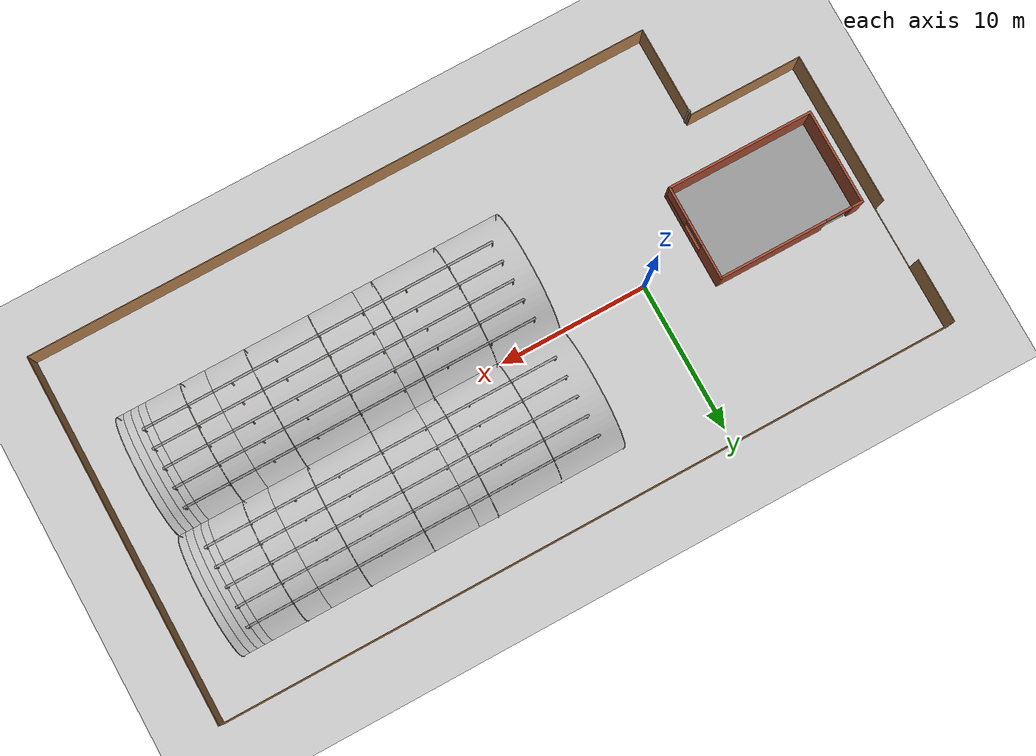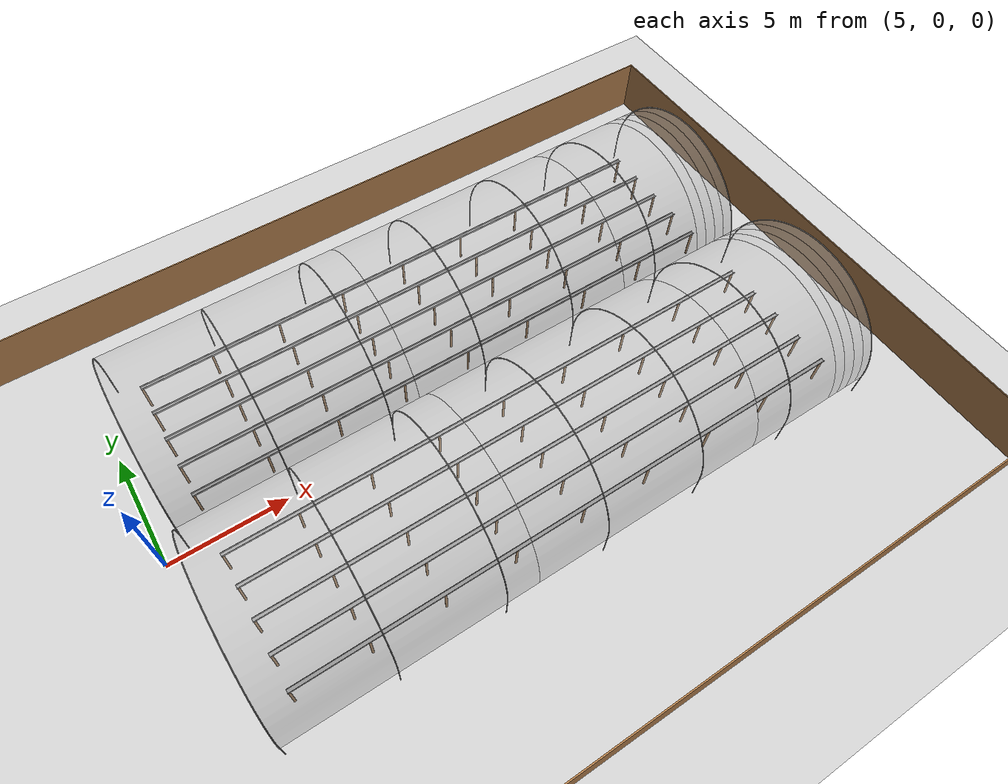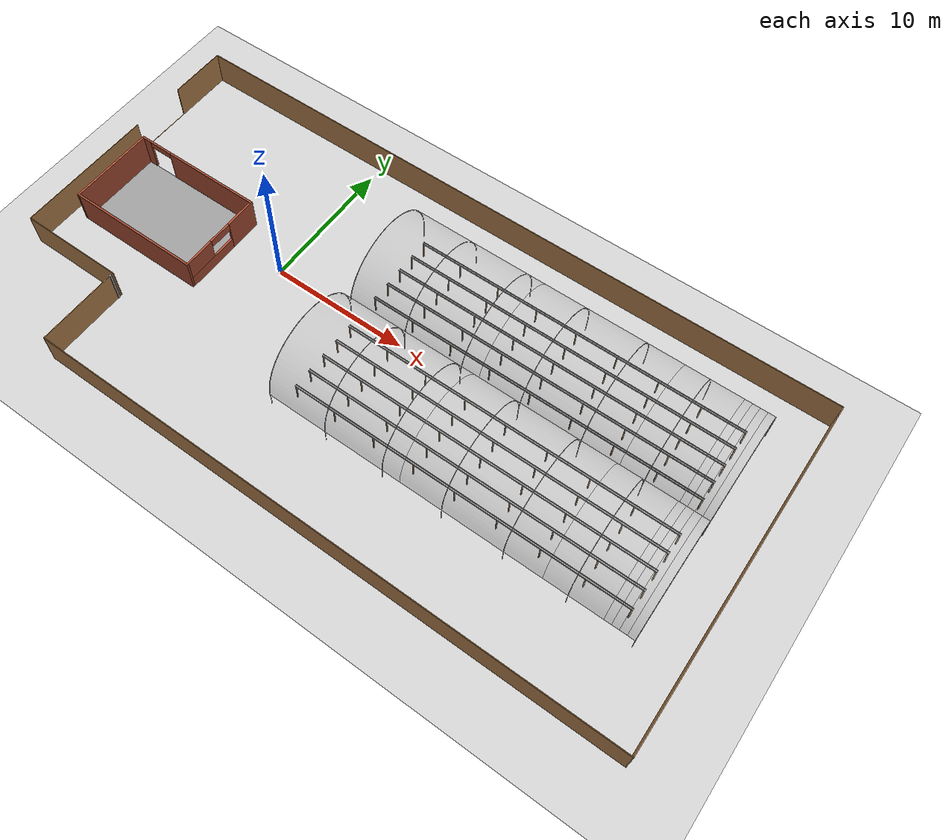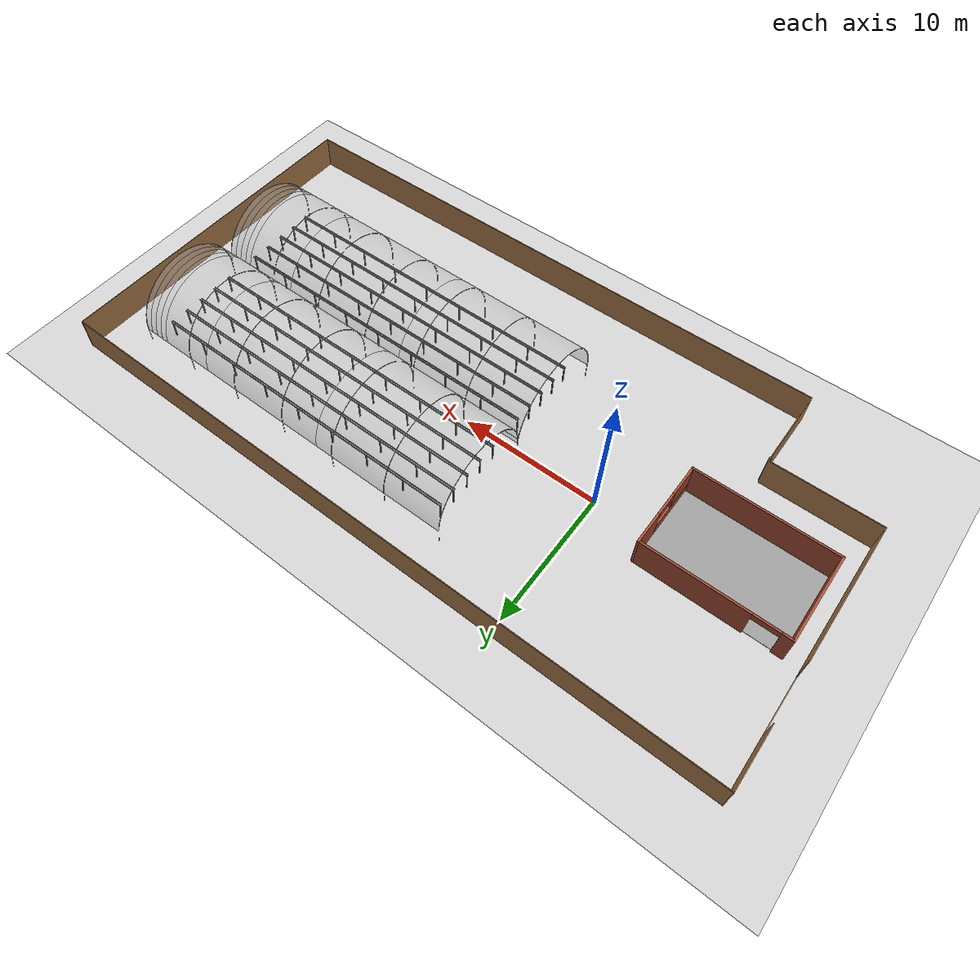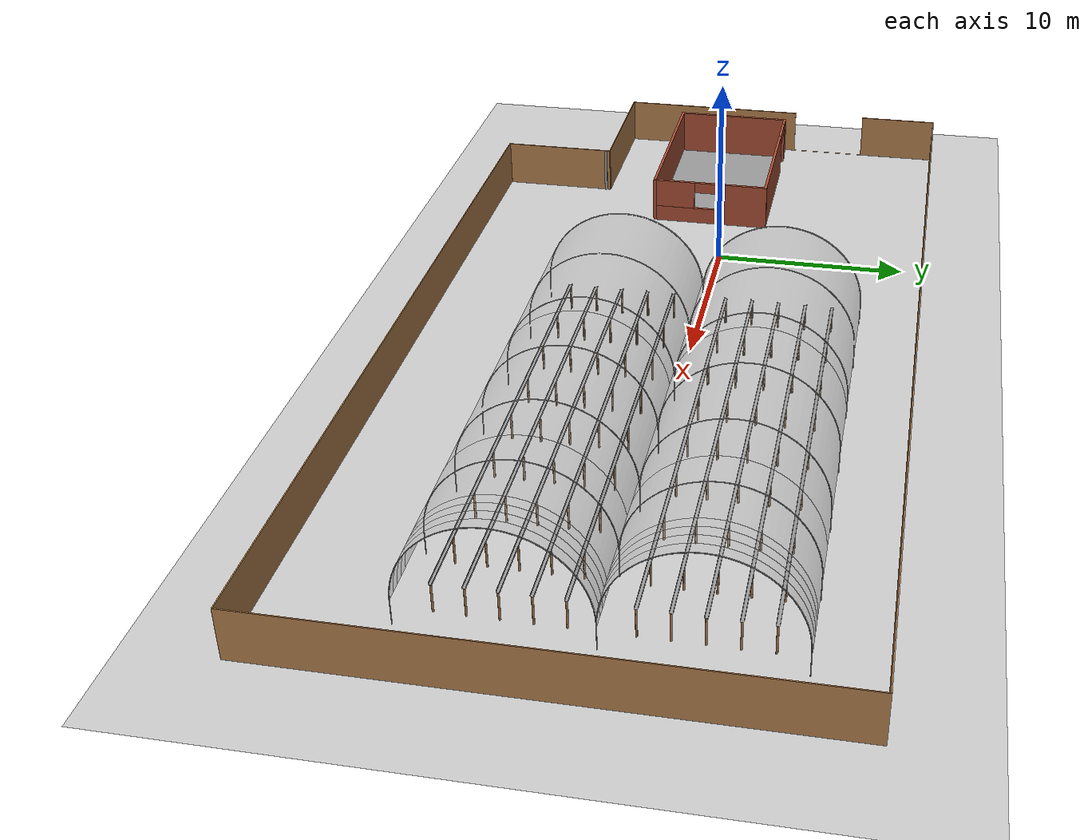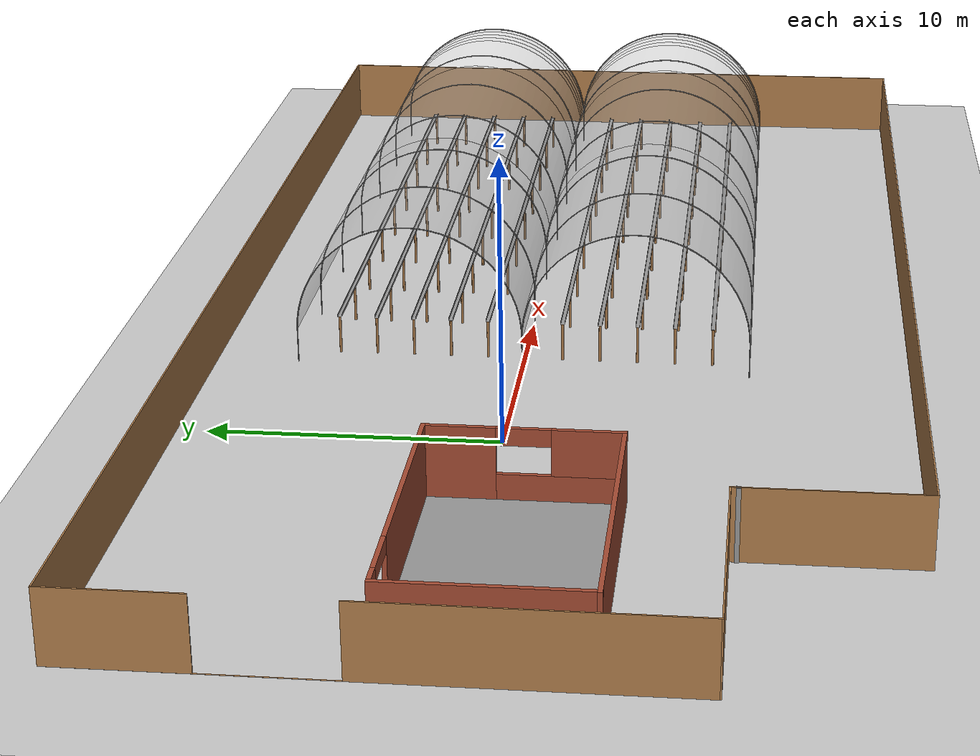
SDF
<sdf version="1.4">
 <world name="default">
  <model name="pole_0">
   <static>1</static>
   <pose>7.000 -6.750 0.691 0.0 0.0 0.0</pose>
   <link name="link">
    <collision name="collision">
     <geometry><cylinder><length>1.38235</length><radius>0.0456111</radius></cylinder></geometry>
    </collision>
    <visual name="visual">
     <geometry><cylinder><length>1.38235</length><radius>0.0456111</radius></cylinder></geometry>
     <material>
      <script><uri>file://media/materials/scripts/gazebo.material</uri><name>Gazebo/WoodFloor</name></script>
      <shader type="vertex"><normal_map>__default__</normal_map></shader>
      <emissive>0 0 0 1</emissive>
      <specular>0.01 0.01 0.01 1</specular>
      <ambient>0.9 0.9 0.9 1</ambient>
      <diffuse>0.09 0.09 0.09 1</diffuse>
     </material>
    </visual>
   </link>
  </model>
  <model name="pole_1">
   <static>1</static>
   <pose>7.000 -5.400 0.691 0.0 0.0 0.0</pose>
   <link name="link">
    <collision name="collision">
     <geometry><cylinder><length>1.38235</length><radius>0.0456111</radius></cylinder></geometry>
    </collision>
    <visual name="visual">
     <geometry><cylinder><length>1.38235</length><radius>0.0456111</radius></cylinder></geometry>
     <material>
      <script><uri>file://media/materials/scripts/gazebo.material</uri><name>Gazebo/WoodFloor</name></script>
      <shader type="vertex"><normal_map>__default__</normal_map></shader>
      <emissive>0 0 0 1</emissive>
      <specular>0.01 0.01 0.01 1</specular>
      <ambient>0.9 0.9 0.9 1</ambient>
      <diffuse>0.09 0.09 0.09 1</diffuse>
     </material>
    </visual>
   </link>
  </model>
  <model name="pole_2">
   <static>1</static>
   <pose>7.000 -4.050 0.691 0.0 0.0 0.0</pose>
   <link name="link">
    <collision name="collision">
     <geometry><cylinder><length>1.38235</length><radius>0.0456111</radius></cylinder></geometry>
    </collision>
    <visual name="visual">
     <geometry><cylinder><length>1.38235</length><radius>0.0456111</radius></cylinder></geometry>
     <material>
      <script><uri>file://media/materials/scripts/gazebo.material</uri><name>Gazebo/WoodFloor</name></script>
      <shader type="vertex"><normal_map>__default__</normal_map></shader>
      <emissive>0 0 0 1</emissive>
      <specular>0.01 0.01 0.01 1</specular>
      <ambient>0.9 0.9 0.9 1</ambient>
      <diffuse>0.09 0.09 0.09 1</diffuse>
     </material>
    </visual>
   </link>
  </model>
  <model name="pole_3">
   <static>1</static>
   <pose>7.000 -2.700 0.691 0.0 0.0 0.0</pose>
   <link name="link">
    <collision name="collision">
     <geometry><cylinder><length>1.38235</length><radius>0.0456111</radius></cylinder></geometry>
    </collision>
    <visual name="visual">
     <geometry><cylinder><length>1.38235</length><radius>0.0456111</radius></cylinder></geometry>
     <material>
      <script><uri>file://media/materials/scripts/gazebo.material</uri><name>Gazebo/WoodFloor</name></script>
      <shader type="vertex"><normal_map>__default__</normal_map></shader>
      <emissive>0 0 0 1</emissive>
      <specular>0.01 0.01 0.01 1</specular>
      <ambient>0.9 0.9 0.9 1</ambient>
      <diffuse>0.09 0.09 0.09 1</diffuse>
     </material>
    </visual>
   </link>
  </model>
  <model name="pole_4">
   <static>1</static>
   <pose>7.000 -1.350 0.691 0.0 0.0 0.0</pose>
   <link name="link">
    <collision name="collision">
     <geometry><cylinder><length>1.38235</length><radius>0.0456111</radius></cylinder></geometry>
    </collision>
    <visual name="visual">
     <geometry><cylinder><length>1.38235</length><radius>0.0456111</radius></cylinder></geometry>
     <material>
      <script><uri>file://media/materials/scripts/gazebo.material</uri><name>Gazebo/WoodFloor</name></script>
      <shader type="vertex"><normal_map>__default__</normal_map></shader>
      <emissive>0 0 0 1</emissive>
      <specular>0.01 0.01 0.01 1</specular>
      <ambient>0.9 0.9 0.9 1</ambient>
      <diffuse>0.09 0.09 0.09 1</diffuse>
     </material>
    </visual>
   </link>
  </model>
  <model name="pole_5">
   <static>1</static>
   <pose>10.000 -6.750 0.691 0.0 0.0 0.0</pose>
   <link name="link">
    <collision name="collision">
     <geometry><cylinder><length>1.38235</length><radius>0.0456111</radius></cylinder></geometry>
    </collision>
    <visual name="visual">
     <geometry><cylinder><length>1.38235</length><radius>0.0456111</radius></cylinder></geometry>
     <material>
      <script><uri>file://media/materials/scripts/gazebo.material</uri><name>Gazebo/WoodFloor</name></script>
      <shader type="vertex"><normal_map>__default__</normal_map></shader>
      <emissive>0 0 0 1</emissive>
      <specular>0.01 0.01 0.01 1</specular>
      <ambient>0.9 0.9 0.9 1</ambient>
      <diffuse>0.09 0.09 0.09 1</diffuse>
     </material>
    </visual>
   </link>
  </model>
  <model name="pole_6">
   <static>1</static>
   <pose>10.000 -5.400 0.691 0.0 0.0 0.0</pose>
   <link name="link">
    <collision name="collision">
     <geometry><cylinder><length>1.38235</length><radius>0.0456111</radius></cylinder></geometry>
    </collision>
    <visual name="visual">
     <geometry><cylinder><length>1.38235</length><radius>0.0456111</radius></cylinder></geometry>
     <material>
      <script><uri>file://media/materials/scripts/gazebo.material</uri><name>Gazebo/WoodFloor</name></script>
      <shader type="vertex"><normal_map>__default__</normal_map></shader>
      <emissive>0 0 0 1</emissive>
      <specular>0.01 0.01 0.01 1</specular>
      <ambient>0.9 0.9 0.9 1</ambient>
      <diffuse>0.09 0.09 0.09 1</diffuse>
     </material>
    </visual>
   </link>
  </model>
  <model name="pole_7">
   <static>1</static>
   <pose>10.000 -4.050 0.691 0.0 0.0 0.0</pose>
   <link name="link">
    <collision name="collision">
     <geometry><cylinder><length>1.38235</length><radius>0.0456111</radius></cylinder></geometry>
    </collision>
    <visual name="visual">
     <geometry><cylinder><length>1.38235</length><radius>0.0456111</radius></cylinder></geometry>
     <material>
      <script><uri>file://media/materials/scripts/gazebo.material</uri><name>Gazebo/WoodFloor</name></script>
      <shader type="vertex"><normal_map>__default__</normal_map></shader>
      <emissive>0 0 0 1</emissive>
      <specular>0.01 0.01 0.01 1</specular>
      <ambient>0.9 0.9 0.9 1</ambient>
      <diffuse>0.09 0.09 0.09 1</diffuse>
     </material>
    </visual>
   </link>
  </model>
  <model name="pole_8">
   <static>1</static>
   <pose>10.000 -2.700 0.691 0.0 0.0 0.0</pose>
   <link name="link">
    <collision name="collision">
     <geometry><cylinder><length>1.38235</length><radius>0.0456111</radius></cylinder></geometry>
    </collision>
    <visual name="visual">
     <geometry><cylinder><length>1.38235</length><radius>0.0456111</radius></cylinder></geometry>
     <material>
      <script><uri>file://media/materials/scripts/gazebo.material</uri><name>Gazebo/WoodFloor</name></script>
      <shader type="vertex"><normal_map>__default__</normal_map></shader>
      <emissive>0 0 0 1</emissive>
      <specular>0.01 0.01 0.01 1</specular>
      <ambient>0.9 0.9 0.9 1</ambient>
      <diffuse>0.09 0.09 0.09 1</diffuse>
     </material>
    </visual>
   </link>
  </model>
  <model name="pole_9">
   <static>1</static>
   <pose>10.000 -1.350 0.691 0.0 0.0 0.0</pose>
   <link name="link">
    <collision name="collision">
     <geometry><cylinder><length>1.38235</length><radius>0.0456111</radius></cylinder></geometry>
    </collision>
    <visual name="visual">
     <geometry><cylinder><length>1.38235</length><radius>0.0456111</radius></cylinder></geometry>
     <material>
      <script><uri>file://media/materials/scripts/gazebo.material</uri><name>Gazebo/WoodFloor</name></script>
      <shader type="vertex"><normal_map>__default__</normal_map></shader>
      <emissive>0 0 0 1</emissive>
      <specular>0.01 0.01 0.01 1</specular>
      <ambient>0.9 0.9 0.9 1</ambient>
      <diffuse>0.09 0.09 0.09 1</diffuse>
     </material>
    </visual>
   </link>
  </model>
  <model name="pole_10">
   <static>1</static>
   <pose>13.000 -6.750 0.691 0.0 0.0 0.0</pose>
   <link name="link">
    <collision name="collision">
     <geometry><cylinder><length>1.38235</length><radius>0.0456111</radius></cylinder></geometry>
    </collision>
    <visual name="visual">
     <geometry><cylinder><length>1.38235</length><radius>0.0456111</radius></cylinder></geometry>
     <material>
      <script><uri>file://media/materials/scripts/gazebo.material</uri><name>Gazebo/WoodFloor</name></script>
      <shader type="vertex"><normal_map>__default__</normal_map></shader>
      <emissive>0 0 0 1</emissive>
      <specular>0.01 0.01 0.01 1</specular>
      <ambient>0.9 0.9 0.9 1</ambient>
      <diffuse>0.09 0.09 0.09 1</diffuse>
     </material>
    </visual>
   </link>
  </model>
  <model name="pole_11">
   <static>1</static>
   <pose>13.000 -5.400 0.691 0.0 0.0 0.0</pose>
   <link name="link">
    <collision name="collision">
     <geometry><cylinder><length>1.38235</length><radius>0.0456111</radius></cylinder></geometry>
    </collision>
    <visual name="visual">
     <geometry><cylinder><length>1.38235</length><radius>0.0456111</radius></cylinder></geometry>
     <material>
      <script><uri>file://media/materials/scripts/gazebo.material</uri><name>Gazebo/WoodFloor</name></script>
      <shader type="vertex"><normal_map>__default__</normal_map></shader>
      <emissive>0 0 0 1</emissive>
      <specular>0.01 0.01 0.01 1</specular>
      <ambient>0.9 0.9 0.9 1</ambient>
      <diffuse>0.09 0.09 0.09 1</diffuse>
     </material>
    </visual>
   </link>
  </model>
  <model name="pole_12">
   <static>1</static>
   <pose>13.000 -4.050 0.691 0.0 0.0 0.0</pose>
   <link name="link">
    <collision name="collision">
     <geometry><cylinder><length>1.38235</length><radius>0.0456111</radius></cylinder></geometry>
    </collision>
    <visual name="visual">
     <geometry><cylinder><length>1.38235</length><radius>0.0456111</radius></cylinder></geometry>
     <material>
      <script><uri>file://media/materials/scripts/gazebo.material</uri><name>Gazebo/WoodFloor</name></script>
      <shader type="vertex"><normal_map>__default__</normal_map></shader>
      <emissive>0 0 0 1</emissive>
      <specular>0.01 0.01 0.01 1</specular>
      <ambient>0.9 0.9 0.9 1</ambient>
      <diffuse>0.09 0.09 0.09 1</diffuse>
     </material>
    </visual>
   </link>
  </model>
  <model name="pole_13">
   <static>1</static>
   <pose>13.000 -2.700 0.691 0.0 0.0 0.0</pose>
   <link name="link">
    <collision name="collision">
     <geometry><cylinder><length>1.38235</length><radius>0.0456111</radius></cylinder></geometry>
    </collision>
    <visual name="visual">
     <geometry><cylinder><length>1.38235</length><radius>0.0456111</radius></cylinder></geometry>
     <material>
      <script><uri>file://media/materials/scripts/gazebo.material</uri><name>Gazebo/WoodFloor</name></script>
      <shader type="vertex"><normal_map>__default__</normal_map></shader>
      <emissive>0 0 0 1</emissive>
      <specular>0.01 0.01 0.01 1</specular>
      <ambient>0.9 0.9 0.9 1</ambient>
      <diffuse>0.09 0.09 0.09 1</diffuse>
     </material>
    </visual>
   </link>
  </model>
  <model name="pole_14">
   <static>1</static>
   <pose>13.000 -1.350 0.691 0.0 0.0 0.0</pose>
   <link name="link">
    <collision name="collision">
     <geometry><cylinder><length>1.38235</length><radius>0.0456111</radius></cylinder></geometry>
    </collision>
    <visual name="visual">
     <geometry><cylinder><length>1.38235</length><radius>0.0456111</radius></cylinder></geometry>
     <material>
      <script><uri>file://media/materials/scripts/gazebo.material</uri><name>Gazebo/WoodFloor</name></script>
      <shader type="vertex"><normal_map>__default__</normal_map></shader>
      <emissive>0 0 0 1</emissive>
      <specular>0.01 0.01 0.01 1</specular>
      <ambient>0.9 0.9 0.9 1</ambient>
      <diffuse>0.09 0.09 0.09 1</diffuse>
     </material>
    </visual>
   </link>
  </model>
  <model name="pole_15">
   <static>1</static>
   <pose>16.000 -6.750 0.691 0.0 0.0 0.0</pose>
   <link name="link">
    <collision name="collision">
     <geometry><cylinder><length>1.38235</length><radius>0.0456111</radius></cylinder></geometry>
    </collision>
    <visual name="visual">
     <geometry><cylinder><length>1.38235</length><radius>0.0456111</radius></cylinder></geometry>
     <material>
      <script><uri>file://media/materials/scripts/gazebo.material</uri><name>Gazebo/WoodFloor</name></script>
      <shader type="vertex"><normal_map>__default__</normal_map></shader>
      <emissive>0 0 0 1</emissive>
      <specular>0.01 0.01 0.01 1</specular>
      <ambient>0.9 0.9 0.9 1</ambient>
      <diffuse>0.09 0.09 0.09 1</diffuse>
     </material>
    </visual>
   </link>
  </model>
  <model name="pole_16">
   <static>1</static>
   <pose>16.000 -5.400 0.691 0.0 0.0 0.0</pose>
   <link name="link">
    <collision name="collision">
     <geometry><cylinder><length>1.38235</length><radius>0.0456111</radius></cylinder></geometry>
    </collision>
    <visual name="visual">
     <geometry><cylinder><length>1.38235</length><radius>0.0456111</radius></cylinder></geometry>
     <material>
      <script><uri>file://media/materials/scripts/gazebo.material</uri><name>Gazebo/WoodFloor</name></script>
      <shader type="vertex"><normal_map>__default__</normal_map></shader>
      <emissive>0 0 0 1</emissive>
      <specular>0.01 0.01 0.01 1</specular>
      <ambient>0.9 0.9 0.9 1</ambient>
      <diffuse>0.09 0.09 0.09 1</diffuse>
     </material>
    </visual>
   </link>
  </model>
  <model name="pole_17">
   <static>1</static>
   <pose>16.000 -4.050 0.691 0.0 0.0 0.0</pose>
   <link name="link">
    <collision name="collision">
     <geometry><cylinder><length>1.38235</length><radius>0.0456111</radius></cylinder></geometry>
    </collision>
    <visual name="visual">
     <geometry><cylinder><length>1.38235</length><radius>0.0456111</radius></cylinder></geometry>
     <material>
      <script><uri>file://media/materials/scripts/gazebo.material</uri><name>Gazebo/WoodFloor</name></script>
      <shader type="vertex"><normal_map>__default__</normal_map></shader>
      <emissive>0 0 0 1</emissive>
      <specular>0.01 0.01 0.01 1</specular>
      <ambient>0.9 0.9 0.9 1</ambient>
      <diffuse>0.09 0.09 0.09 1</diffuse>
     </material>
    </visual>
   </link>
  </model>
  <model name="pole_18">
   <static>1</static>
   <pose>16.000 -2.700 0.691 0.0 0.0 0.0</pose>
   <link name="link">
    <collision name="collision">
     <geometry><cylinder><length>1.38235</length><radius>0.0456111</radius></cylinder></geometry>
    </collision>
    <visual name="visual">
     <geometry><cylinder><length>1.38235</length><radius>0.0456111</radius></cylinder></geometry>
     <material>
      <script><uri>file://media/materials/scripts/gazebo.material</uri><name>Gazebo/WoodFloor</name></script>
      <shader type="vertex"><normal_map>__default__</normal_map></shader>
      <emissive>0 0 0 1</emissive>
      <specular>0.01 0.01 0.01 1</specular>
      <ambient>0.9 0.9 0.9 1</ambient>
      <diffuse>0.09 0.09 0.09 1</diffuse>
     </material>
    </visual>
   </link>
  </model>
  <model name="pole_19">
   <static>1</static>
   <pose>16.000 -1.350 0.691 0.0 0.0 0.0</pose>
   <link name="link">
    <collision name="collision">
     <geometry><cylinder><length>1.38235</length><radius>0.0456111</radius></cylinder></geometry>
    </collision>
    <visual name="visual">
     <geometry><cylinder><length>1.38235</length><radius>0.0456111</radius></cylinder></geometry>
     <material>
      <script><uri>file://media/materials/scripts/gazebo.material</uri><name>Gazebo/WoodFloor</name></script>
      <shader type="vertex"><normal_map>__default__</normal_map></shader>
      <emissive>0 0 0 1</emissive>
      <specular>0.01 0.01 0.01 1</specular>
      <ambient>0.9 0.9 0.9 1</ambient>
      <diffuse>0.09 0.09 0.09 1</diffuse>
     </material>
    </visual>
   </link>
  </model>
  <model name="pole_20">
   <static>1</static>
   <pose>19.000 -6.750 0.691 0.0 0.0 0.0</pose>
   <link name="link">
    <collision name="collision">
     <geometry><cylinder><length>1.38235</length><radius>0.0456111</radius></cylinder></geometry>
    </collision>
    <visual name="visual">
     <geometry><cylinder><length>1.38235</length><radius>0.0456111</radius></cylinder></geometry>
     <material>
      <script><uri>file://media/materials/scripts/gazebo.material</uri><name>Gazebo/WoodFloor</name></script>
      <shader type="vertex"><normal_map>__default__</normal_map></shader>
      <emissive>0 0 0 1</emissive>
      <specular>0.01 0.01 0.01 1</specular>
      <ambient>0.9 0.9 0.9 1</ambient>
      <diffuse>0.09 0.09 0.09 1</diffuse>
     </material>
    </visual>
   </link>
  </model>
  <model name="pole_21">
   <static>1</static>
   <pose>19.000 -5.400 0.691 0.0 0.0 0.0</pose>
   <link name="link">
    <collision name="collision">
     <geometry><cylinder><length>1.38235</length><radius>0.0456111</radius></cylinder></geometry>
    </collision>
    <visual name="visual">
     <geometry><cylinder><length>1.38235</length><radius>0.0456111</radius></cylinder></geometry>
     <material>
      <script><uri>file://media/materials/scripts/gazebo.material</uri><name>Gazebo/WoodFloor</name></script>
      <shader type="vertex"><normal_map>__default__</normal_map></shader>
      <emissive>0 0 0 1</emissive>
      <specular>0.01 0.01 0.01 1</specular>
      <ambient>0.9 0.9 0.9 1</ambient>
      <diffuse>0.09 0.09 0.09 1</diffuse>
     </material>
    </visual>
   </link>
  </model>
  <model name="pole_22">
   <static>1</static>
   <pose>19.000 -4.050 0.691 0.0 0.0 0.0</pose>
   <link name="link">
    <collision name="collision">
     <geometry><cylinder><length>1.38235</length><radius>0.0456111</radius></cylinder></geometry>
    </collision>
    <visual name="visual">
     <geometry><cylinder><length>1.38235</length><radius>0.0456111</radius></cylinder></geometry>
     <material>
      <script><uri>file://media/materials/scripts/gazebo.material</uri><name>Gazebo/WoodFloor</name></script>
      <shader type="vertex"><normal_map>__default__</normal_map></shader>
      <emissive>0 0 0 1</emissive>
      <specular>0.01 0.01 0.01 1</specular>
      <ambient>0.9 0.9 0.9 1</ambient>
      <diffuse>0.09 0.09 0.09 1</diffuse>
     </material>
    </visual>
   </link>
  </model>
  <model name="pole_23">
   <static>1</static>
   <pose>19.000 -2.700 0.691 0.0 0.0 0.0</pose>
   <link name="link">
    <collision name="collision">
     <geometry><cylinder><length>1.38235</length><radius>0.0456111</radius></cylinder></geometry>
    </collision>
    <visual name="visual">
     <geometry><cylinder><length>1.38235</length><radius>0.0456111</radius></cylinder></geometry>
     <material>
      <script><uri>file://media/materials/scripts/gazebo.material</uri><name>Gazebo/WoodFloor</name></script>
      <shader type="vertex"><normal_map>__default__</normal_map></shader>
      <emissive>0 0 0 1</emissive>
      <specular>0.01 0.01 0.01 1</specular>
      <ambient>0.9 0.9 0.9 1</ambient>
      <diffuse>0.09 0.09 0.09 1</diffuse>
     </material>
    </visual>
   </link>
  </model>
  <model name="pole_24">
   <static>1</static>
   <pose>19.000 -1.350 0.691 0.0 0.0 0.0</pose>
   <link name="link">
    <collision name="collision">
     <geometry><cylinder><length>1.38235</length><radius>0.0456111</radius></cylinder></geometry>
    </collision>
    <visual name="visual">
     <geometry><cylinder><length>1.38235</length><radius>0.0456111</radius></cylinder></geometry>
     <material>
      <script><uri>file://media/materials/scripts/gazebo.material</uri><name>Gazebo/WoodFloor</name></script>
      <shader type="vertex"><normal_map>__default__</normal_map></shader>
      <emissive>0 0 0 1</emissive>
      <specular>0.01 0.01 0.01 1</specular>
      <ambient>0.9 0.9 0.9 1</ambient>
      <diffuse>0.09 0.09 0.09 1</diffuse>
     </material>
    </visual>
   </link>
  </model>
  <model name="pole_25">
   <static>1</static>
   <pose>22.000 -6.750 0.691 0.0 0.0 0.0</pose>
   <link name="link">
    <collision name="collision">
     <geometry><cylinder><length>1.38235</length><radius>0.0456111</radius></cylinder></geometry>
    </collision>
    <visual name="visual">
     <geometry><cylinder><length>1.38235</length><radius>0.0456111</radius></cylinder></geometry>
     <material>
      <script><uri>file://media/materials/scripts/gazebo.material</uri><name>Gazebo/WoodFloor</name></script>
      <shader type="vertex"><normal_map>__default__</normal_map></shader>
      <emissive>0 0 0 1</emissive>
      <specular>0.01 0.01 0.01 1</specular>
      <ambient>0.9 0.9 0.9 1</ambient>
      <diffuse>0.09 0.09 0.09 1</diffuse>
     </material>
    </visual>
   </link>
  </model>
  <model name="pole_26">
   <static>1</static>
   <pose>22.000 -5.400 0.691 0.0 0.0 0.0</pose>
   <link name="link">
    <collision name="collision">
     <geometry><cylinder><length>1.38235</length><radius>0.0456111</radius></cylinder></geometry>
    </collision>
    <visual name="visual">
     <geometry><cylinder><length>1.38235</length><radius>0.0456111</radius></cylinder></geometry>
     <material>
      <script><uri>file://media/materials/scripts/gazebo.material</uri><name>Gazebo/WoodFloor</name></script>
      <shader type="vertex"><normal_map>__default__</normal_map></shader>
      <emissive>0 0 0 1</emissive>
      <specular>0.01 0.01 0.01 1</specular>
      <ambient>0.9 0.9 0.9 1</ambient>
      <diffuse>0.09 0.09 0.09 1</diffuse>
     </material>
    </visual>
   </link>
  </model>
  <model name="pole_27">
   <static>1</static>
   <pose>22.000 -4.050 0.691 0.0 0.0 0.0</pose>
   <link name="link">
    <collision name="collision">
     <geometry><cylinder><length>1.38235</length><radius>0.0456111</radius></cylinder></geometry>
    </collision>
    <visual name="visual">
     <geometry><cylinder><length>1.38235</length><radius>0.0456111</radius></cylinder></geometry>
     <material>
      <script><uri>file://media/materials/scripts/gazebo.material</uri><name>Gazebo/WoodFloor</name></script>
      <shader type="vertex"><normal_map>__default__</normal_map></shader>
      <emissive>0 0 0 1</emissive>
      <specular>0.01 0.01 0.01 1</specular>
      <ambient>0.9 0.9 0.9 1</ambient>
      <diffuse>0.09 0.09 0.09 1</diffuse>
     </material>
    </visual>
   </link>
  </model>
  <model name="pole_28">
   <static>1</static>
   <pose>22.000 -2.700 0.691 0.0 0.0 0.0</pose>
   <link name="link">
    <collision name="collision">
     <geometry><cylinder><length>1.38235</length><radius>0.0456111</radius></cylinder></geometry>
    </collision>
    <visual name="visual">
     <geometry><cylinder><length>1.38235</length><radius>0.0456111</radius></cylinder></geometry>
     <material>
      <script><uri>file://media/materials/scripts/gazebo.material</uri><name>Gazebo/WoodFloor</name></script>
      <shader type="vertex"><normal_map>__default__</normal_map></shader>
      <emissive>0 0 0 1</emissive>
      <specular>0.01 0.01 0.01 1</specular>
      <ambient>0.9 0.9 0.9 1</ambient>
      <diffuse>0.09 0.09 0.09 1</diffuse>
     </material>
    </visual>
   </link>
  </model>
  <model name="pole_29">
   <static>1</static>
   <pose>22.000 -1.350 0.691 0.0 0.0 0.0</pose>
   <link name="link">
    <collision name="collision">
     <geometry><cylinder><length>1.38235</length><radius>0.0456111</radius></cylinder></geometry>
    </collision>
    <visual name="visual">
     <geometry><cylinder><length>1.38235</length><radius>0.0456111</radius></cylinder></geometry>
     <material>
      <script><uri>file://media/materials/scripts/gazebo.material</uri><name>Gazebo/WoodFloor</name></script>
      <shader type="vertex"><normal_map>__default__</normal_map></shader>
      <emissive>0 0 0 1</emissive>
      <specular>0.01 0.01 0.01 1</specular>
      <ambient>0.9 0.9 0.9 1</ambient>
      <diffuse>0.09 0.09 0.09 1</diffuse>
     </material>
    </visual>
   </link>
  </model>
  <model name="pole_30">
   <static>1</static>
   <pose>25.000 -6.750 0.691 0.0 0.0 0.0</pose>
   <link name="link">
    <collision name="collision">
     <geometry><cylinder><length>1.38235</length><radius>0.0456111</radius></cylinder></geometry>
    </collision>
    <visual name="visual">
     <geometry><cylinder><length>1.38235</length><radius>0.0456111</radius></cylinder></geometry>
     <material>
      <script><uri>file://media/materials/scripts/gazebo.material</uri><name>Gazebo/WoodFloor</name></script>
      <shader type="vertex"><normal_map>__default__</normal_map></shader>
      <emissive>0 0 0 1</emissive>
      <specular>0.01 0.01 0.01 1</specular>
      <ambient>0.9 0.9 0.9 1</ambient>
      <diffuse>0.09 0.09 0.09 1</diffuse>
     </material>
    </visual>
   </link>
  </model>
  <model name="pole_31">
   <static>1</static>
   <pose>25.000 -5.400 0.691 0.0 0.0 0.0</pose>
   <link name="link">
    <collision name="collision">
     <geometry><cylinder><length>1.38235</length><radius>0.0456111</radius></cylinder></geometry>
    </collision>
    <visual name="visual">
     <geometry><cylinder><length>1.38235</length><radius>0.0456111</radius></cylinder></geometry>
     <material>
      <script><uri>file://media/materials/scripts/gazebo.material</uri><name>Gazebo/WoodFloor</name></script>
      <shader type="vertex"><normal_map>__default__</normal_map></shader>
      <emissive>0 0 0 1</emissive>
      <specular>0.01 0.01 0.01 1</specular>
      <ambient>0.9 0.9 0.9 1</ambient>
      <diffuse>0.09 0.09 0.09 1</diffuse>
     </material>
    </visual>
   </link>
  </model>
  <model name="pole_32">
   <static>1</static>
   <pose>25.000 -4.050 0.691 0.0 0.0 0.0</pose>
   <link name="link">
    <collision name="collision">
     <geometry><cylinder><length>1.38235</length><radius>0.0456111</radius></cylinder></geometry>
    </collision>
    <visual name="visual">
     <geometry><cylinder><length>1.38235</length><radius>0.0456111</radius></cylinder></geometry>
     <material>
      <script><uri>file://media/materials/scripts/gazebo.material</uri><name>Gazebo/WoodFloor</name></script>
      <shader type="vertex"><normal_map>__default__</normal_map></shader>
      <emissive>0 0 0 1</emissive>
      <specular>0.01 0.01 0.01 1</specular>
      <ambient>0.9 0.9 0.9 1</ambient>
      <diffuse>0.09 0.09 0.09 1</diffuse>
     </material>
    </visual>
   </link>
  </model>
  <model name="pole_33">
   <static>1</static>
   <pose>25.000 -2.700 0.691 0.0 0.0 0.0</pose>
   <link name="link">
    <collision name="collision">
     <geometry><cylinder><length>1.38235</length><radius>0.0456111</radius></cylinder></geometry>
    </collision>
    <visual name="visual">
     <geometry><cylinder><length>1.38235</length><radius>0.0456111</radius></cylinder></geometry>
     <material>
      <script><uri>file://media/materials/scripts/gazebo.material</uri><name>Gazebo/WoodFloor</name></script>
      <shader type="vertex"><normal_map>__default__</normal_map></shader>
      <emissive>0 0 0 1</emissive>
      <specular>0.01 0.01 0.01 1</specular>
      <ambient>0.9 0.9 0.9 1</ambient>
      <diffuse>0.09 0.09 0.09 1</diffuse>
     </material>
    </visual>
   </link>
  </model>
  <model name="pole_34">
   <static>1</static>
   <pose>25.000 -1.350 0.691 0.0 0.0 0.0</pose>
   <link name="link">
    <collision name="collision">
     <geometry><cylinder><length>1.38235</length><radius>0.0456111</radius></cylinder></geometry>
    </collision>
    <visual name="visual">
     <geometry><cylinder><length>1.38235</length><radius>0.0456111</radius></cylinder></geometry>
     <material>
      <script><uri>file://media/materials/scripts/gazebo.material</uri><name>Gazebo/WoodFloor</name></script>
      <shader type="vertex"><normal_map>__default__</normal_map></shader>
      <emissive>0 0 0 1</emissive>
      <specular>0.01 0.01 0.01 1</specular>
      <ambient>0.9 0.9 0.9 1</ambient>
      <diffuse>0.09 0.09 0.09 1</diffuse>
     </material>
    </visual>
   </link>
  </model>
  <model name="pole_35">
   <static>1</static>
   <pose>28.000 -6.750 0.691 0.0 0.0 0.0</pose>
   <link name="link">
    <collision name="collision">
     <geometry><cylinder><length>1.38235</length><radius>0.0456111</radius></cylinder></geometry>
    </collision>
    <visual name="visual">
     <geometry><cylinder><length>1.38235</length><radius>0.0456111</radius></cylinder></geometry>
     <material>
      <script><uri>file://media/materials/scripts/gazebo.material</uri><name>Gazebo/WoodFloor</name></script>
      <shader type="vertex"><normal_map>__default__</normal_map></shader>
      <emissive>0 0 0 1</emissive>
      <specular>0.01 0.01 0.01 1</specular>
      <ambient>0.9 0.9 0.9 1</ambient>
      <diffuse>0.09 0.09 0.09 1</diffuse>
     </material>
    </visual>
   </link>
  </model>
  <model name="pole_36">
   <static>1</static>
   <pose>28.000 -5.400 0.691 0.0 0.0 0.0</pose>
   <link name="link">
    <collision name="collision">
     <geometry><cylinder><length>1.38235</length><radius>0.0456111</radius></cylinder></geometry>
    </collision>
    <visual name="visual">
     <geometry><cylinder><length>1.38235</length><radius>0.0456111</radius></cylinder></geometry>
     <material>
      <script><uri>file://media/materials/scripts/gazebo.material</uri><name>Gazebo/WoodFloor</name></script>
      <shader type="vertex"><normal_map>__default__</normal_map></shader>
      <emissive>0 0 0 1</emissive>
      <specular>0.01 0.01 0.01 1</specular>
      <ambient>0.9 0.9 0.9 1</ambient>
      <diffuse>0.09 0.09 0.09 1</diffuse>
     </material>
    </visual>
   </link>
  </model>
  <model name="pole_37">
   <static>1</static>
   <pose>28.000 -4.050 0.691 0.0 0.0 0.0</pose>
   <link name="link">
    <collision name="collision">
     <geometry><cylinder><length>1.38235</length><radius>0.0456111</radius></cylinder></geometry>
    </collision>
    <visual name="visual">
     <geometry><cylinder><length>1.38235</length><radius>0.0456111</radius></cylinder></geometry>
     <material>
      <script><uri>file://media/materials/scripts/gazebo.material</uri><name>Gazebo/WoodFloor</name></script>
      <shader type="vertex"><normal_map>__default__</normal_map></shader>
      <emissive>0 0 0 1</emissive>
      <specular>0.01 0.01 0.01 1</specular>
      <ambient>0.9 0.9 0.9 1</ambient>
      <diffuse>0.09 0.09 0.09 1</diffuse>
     </material>
    </visual>
   </link>
  </model>
  <model name="pole_38">
   <static>1</static>
   <pose>28.000 -2.700 0.691 0.0 0.0 0.0</pose>
   <link name="link">
    <collision name="collision">
     <geometry><cylinder><length>1.38235</length><radius>0.0456111</radius></cylinder></geometry>
    </collision>
    <visual name="visual">
     <geometry><cylinder><length>1.38235</length><radius>0.0456111</radius></cylinder></geometry>
     <material>
      <script><uri>file://media/materials/scripts/gazebo.material</uri><name>Gazebo/WoodFloor</name></script>
      <shader type="vertex"><normal_map>__default__</normal_map></shader>
      <emissive>0 0 0 1</emissive>
      <specular>0.01 0.01 0.01 1</specular>
      <ambient>0.9 0.9 0.9 1</ambient>
      <diffuse>0.09 0.09 0.09 1</diffuse>
     </material>
    </visual>
   </link>
  </model>
  <model name="pole_39">
   <static>1</static>
   <pose>28.000 -1.350 0.691 0.0 0.0 0.0</pose>
   <link name="link">
    <collision name="collision">
     <geometry><cylinder><length>1.38235</length><radius>0.0456111</radius></cylinder></geometry>
    </collision>
    <visual name="visual">
     <geometry><cylinder><length>1.38235</length><radius>0.0456111</radius></cylinder></geometry>
     <material>
      <script><uri>file://media/materials/scripts/gazebo.material</uri><name>Gazebo/WoodFloor</name></script>
      <shader type="vertex"><normal_map>__default__</normal_map></shader>
      <emissive>0 0 0 1</emissive>
      <specular>0.01 0.01 0.01 1</specular>
      <ambient>0.9 0.9 0.9 1</ambient>
      <diffuse>0.09 0.09 0.09 1</diffuse>
     </material>
    </visual>
   </link>
  </model>
  <model name="pole_40">
   <static>1</static>
   <pose>31.000 -6.750 0.691 0.0 0.0 0.0</pose>
   <link name="link">
    <collision name="collision">
     <geometry><cylinder><length>1.38235</length><radius>0.0456111</radius></cylinder></geometry>
    </collision>
    <visual name="visual">
     <geometry><cylinder><length>1.38235</length><radius>0.0456111</radius></cylinder></geometry>
     <material>
      <script><uri>file://media/materials/scripts/gazebo.material</uri><name>Gazebo/WoodFloor</name></script>
      <shader type="vertex"><normal_map>__default__</normal_map></shader>
      <emissive>0 0 0 1</emissive>
      <specular>0.01 0.01 0.01 1</specular>
      <ambient>0.9 0.9 0.9 1</ambient>
      <diffuse>0.09 0.09 0.09 1</diffuse>
     </material>
    </visual>
   </link>
  </model>
  <model name="pole_41">
   <static>1</static>
   <pose>31.000 -5.400 0.691 0.0 0.0 0.0</pose>
   <link name="link">
    <collision name="collision">
     <geometry><cylinder><length>1.38235</length><radius>0.0456111</radius></cylinder></geometry>
    </collision>
    <visual name="visual">
     <geometry><cylinder><length>1.38235</length><radius>0.0456111</radius></cylinder></geometry>
     <material>
      <script><uri>file://media/materials/scripts/gazebo.material</uri><name>Gazebo/WoodFloor</name></script>
      <shader type="vertex"><normal_map>__default__</normal_map></shader>
      <emissive>0 0 0 1</emissive>
      <specular>0.01 0.01 0.01 1</specular>
      <ambient>0.9 0.9 0.9 1</ambient>
      <diffuse>0.09 0.09 0.09 1</diffuse>
     </material>
    </visual>
   </link>
  </model>
  <model name="pole_42">
   <static>1</static>
   <pose>31.000 -4.050 0.691 0.0 0.0 0.0</pose>
   <link name="link">
    <collision name="collision">
     <geometry><cylinder><length>1.38235</length><radius>0.0456111</radius></cylinder></geometry>
    </collision>
    <visual name="visual">
     <geometry><cylinder><length>1.38235</length><radius>0.0456111</radius></cylinder></geometry>
     <material>
      <script><uri>file://media/materials/scripts/gazebo.material</uri><name>Gazebo/WoodFloor</name></script>
      <shader type="vertex"><normal_map>__default__</normal_map></shader>
      <emissive>0 0 0 1</emissive>
      <specular>0.01 0.01 0.01 1</specular>
      <ambient>0.9 0.9 0.9 1</ambient>
      <diffuse>0.09 0.09 0.09 1</diffuse>
     </material>
    </visual>
   </link>
  </model>
  <model name="pole_43">
   <static>1</static>
   <pose>31.000 -2.700 0.691 0.0 0.0 0.0</pose>
   <link name="link">
    <collision name="collision">
     <geometry><cylinder><length>1.38235</length><radius>0.0456111</radius></cylinder></geometry>
    </collision>
    <visual name="visual">
     <geometry><cylinder><length>1.38235</length><radius>0.0456111</radius></cylinder></geometry>
     <material>
      <script><uri>file://media/materials/scripts/gazebo.material</uri><name>Gazebo/WoodFloor</name></script>
      <shader type="vertex"><normal_map>__default__</normal_map></shader>
      <emissive>0 0 0 1</emissive>
      <specular>0.01 0.01 0.01 1</specular>
      <ambient>0.9 0.9 0.9 1</ambient>
      <diffuse>0.09 0.09 0.09 1</diffuse>
     </material>
    </visual>
   </link>
  </model>
  <model name="pole_44">
   <static>1</static>
   <pose>31.000 -1.350 0.691 0.0 0.0 0.0</pose>
   <link name="link">
    <collision name="collision">
     <geometry><cylinder><length>1.38235</length><radius>0.0456111</radius></cylinder></geometry>
    </collision>
    <visual name="visual">
     <geometry><cylinder><length>1.38235</length><radius>0.0456111</radius></cylinder></geometry>
     <material>
      <script><uri>file://media/materials/scripts/gazebo.material</uri><name>Gazebo/WoodFloor</name></script>
      <shader type="vertex"><normal_map>__default__</normal_map></shader>
      <emissive>0 0 0 1</emissive>
      <specular>0.01 0.01 0.01 1</specular>
      <ambient>0.9 0.9 0.9 1</ambient>
      <diffuse>0.09 0.09 0.09 1</diffuse>
     </material>
    </visual>
   </link>
  </model>
  <model name="tray_0">
   <static>1</static>
   <link name="link_0">
    <collision name="collision"><geometry><box><size>24.100 0.15 0.005</size></box></geometry></collision>
    <visual name="visual">
     <geometry><box><size>24.100 0.15 0.005</size></box></geometry>
     <material>
      <script><uri>file://media/materials/scripts/gazebo.material</uri><name>Gazebo/Grey</name></script>
      <emissive>0 0 0 1</emissive>
      <shader type="vertex"><normal_map>__default__</normal_map></shader>
      <specular>0.01 0.01 0.01 1</specular>
      <lighting>1</lighting>
      <ambient>0.7 0.7 0.7 1</ambient>
      <diffuse>0.3 0.3 0.3 1</diffuse>
     </material>
    </visual>
    <pose>19.000 -6.750 1.382 0.0 0.0 0.0</pose>
   </link>
  </model>
  <model name="tray_1">
   <static>1</static>
   <link name="link_0">
    <collision name="collision"><geometry><box><size>24.100 0.15 0.005</size></box></geometry></collision>
    <visual name="visual">
     <geometry><box><size>24.100 0.15 0.005</size></box></geometry>
     <material>
      <script><uri>file://media/materials/scripts/gazebo.material</uri><name>Gazebo/Grey</name></script>
      <emissive>0 0 0 1</emissive>
      <shader type="vertex"><normal_map>__default__</normal_map></shader>
      <specular>0.01 0.01 0.01 1</specular>
      <lighting>1</lighting>
      <ambient>0.7 0.7 0.7 1</ambient>
      <diffuse>0.3 0.3 0.3 1</diffuse>
     </material>
    </visual>
    <pose>19.000 -5.400 1.382 0.0 0.0 0.0</pose>
   </link>
  </model>
  <model name="tray_2">
   <static>1</static>
   <link name="link_0">
    <collision name="collision"><geometry><box><size>24.100 0.15 0.005</size></box></geometry></collision>
    <visual name="visual">
     <geometry><box><size>24.100 0.15 0.005</size></box></geometry>
     <material>
      <script><uri>file://media/materials/scripts/gazebo.material</uri><name>Gazebo/Grey</name></script>
      <emissive>0 0 0 1</emissive>
      <shader type="vertex"><normal_map>__default__</normal_map></shader>
      <specular>0.01 0.01 0.01 1</specular>
      <lighting>1</lighting>
      <ambient>0.7 0.7 0.7 1</ambient>
      <diffuse>0.3 0.3 0.3 1</diffuse>
     </material>
    </visual>
    <pose>19.000 -4.050 1.382 0.0 0.0 0.0</pose>
   </link>
  </model>
  <model name="tray_3">
   <static>1</static>
   <link name="link_0">
    <collision name="collision"><geometry><box><size>24.100 0.15 0.005</size></box></geometry></collision>
    <visual name="visual">
     <geometry><box><size>24.100 0.15 0.005</size></box></geometry>
     <material>
      <script><uri>file://media/materials/scripts/gazebo.material</uri><name>Gazebo/Grey</name></script>
      <emissive>0 0 0 1</emissive>
      <shader type="vertex"><normal_map>__default__</normal_map></shader>
      <specular>0.01 0.01 0.01 1</specular>
      <lighting>1</lighting>
      <ambient>0.7 0.7 0.7 1</ambient>
      <diffuse>0.3 0.3 0.3 1</diffuse>
     </material>
    </visual>
    <pose>19.000 -2.700 1.382 0.0 0.0 0.0</pose>
   </link>
  </model>
  <model name="tray_4">
   <static>1</static>
   <link name="link_0">
    <collision name="collision"><geometry><box><size>24.100 0.15 0.005</size></box></geometry></collision>
    <visual name="visual">
     <geometry><box><size>24.100 0.15 0.005</size></box></geometry>
     <material>
      <script><uri>file://media/materials/scripts/gazebo.material</uri><name>Gazebo/Grey</name></script>
      <emissive>0 0 0 1</emissive>
      <shader type="vertex"><normal_map>__default__</normal_map></shader>
      <specular>0.01 0.01 0.01 1</specular>
      <lighting>1</lighting>
      <ambient>0.7 0.7 0.7 1</ambient>
      <diffuse>0.3 0.3 0.3 1</diffuse>
     </material>
    </visual>
    <pose>19.000 -1.350 1.382 0.0 0.0 0.0</pose>
   </link>
  </model>
  <model name="tray_p2_0">
   <static>1</static>
   <link name="link_0">
    <collision name="collision"><geometry><box><size>24.10 0.085 0.005</size></box></geometry></collision>
    <visual name="visual">
     <geometry><box><size>24.10 0.085 0.005</size></box></geometry>
     <material>
      <script><uri>file://media/materials/scripts/gazebo.material</uri><name>Gazebo/Grey</name></script>
      <emissive>0 0 0 1</emissive>
      <shader type="vertex"><normal_map>__default__</normal_map></shader>
      <specular>0.01 0.01 0.01 1</specular>
      <lighting>1</lighting>
      <ambient>0.7 0.7 0.7 1</ambient>
      <diffuse>0.3 0.3 0.3 1</diffuse>
     </material>
    </visual>
    <pose>19.000 -6.825 1.424 1.5707 0.0 0.0</pose>
   </link>
  </model>
  <model name="tray_p2_1">
   <static>1</static>
   <link name="link_0">
    <collision name="collision"><geometry><box><size>24.10 0.085 0.005</size></box></geometry></collision>
    <visual name="visual">
     <geometry><box><size>24.10 0.085 0.005</size></box></geometry>
     <material>
      <script><uri>file://media/materials/scripts/gazebo.material</uri><name>Gazebo/Grey</name></script>
      <emissive>0 0 0 1</emissive>
      <shader type="vertex"><normal_map>__default__</normal_map></shader>
      <specular>0.01 0.01 0.01 1</specular>
      <lighting>1</lighting>
      <ambient>0.7 0.7 0.7 1</ambient>
      <diffuse>0.3 0.3 0.3 1</diffuse>
     </material>
    </visual>
    <pose>19.000 -5.475 1.424 1.5707 0.0 0.0</pose>
   </link>
  </model>
  <model name="tray_p2_2">
   <static>1</static>
   <link name="link_0">
    <collision name="collision"><geometry><box><size>24.10 0.085 0.005</size></box></geometry></collision>
    <visual name="visual">
     <geometry><box><size>24.10 0.085 0.005</size></box></geometry>
     <material>
      <script><uri>file://media/materials/scripts/gazebo.material</uri><name>Gazebo/Grey</name></script>
      <emissive>0 0 0 1</emissive>
      <shader type="vertex"><normal_map>__default__</normal_map></shader>
      <specular>0.01 0.01 0.01 1</specular>
      <lighting>1</lighting>
      <ambient>0.7 0.7 0.7 1</ambient>
      <diffuse>0.3 0.3 0.3 1</diffuse>
     </material>
    </visual>
    <pose>19.000 -4.125 1.424 1.5707 0.0 0.0</pose>
   </link>
  </model>
  <model name="tray_p2_3">
   <static>1</static>
   <link name="link_0">
    <collision name="collision"><geometry><box><size>24.10 0.085 0.005</size></box></geometry></collision>
    <visual name="visual">
     <geometry><box><size>24.10 0.085 0.005</size></box></geometry>
     <material>
      <script><uri>file://media/materials/scripts/gazebo.material</uri><name>Gazebo/Grey</name></script>
      <emissive>0 0 0 1</emissive>
      <shader type="vertex"><normal_map>__default__</normal_map></shader>
      <specular>0.01 0.01 0.01 1</specular>
      <lighting>1</lighting>
      <ambient>0.7 0.7 0.7 1</ambient>
      <diffuse>0.3 0.3 0.3 1</diffuse>
     </material>
    </visual>
    <pose>19.000 -2.775 1.424 1.5707 0.0 0.0</pose>
   </link>
  </model>
  <model name="tray_p2_4">
   <static>1</static>
   <link name="link_0">
    <collision name="collision"><geometry><box><size>24.10 0.085 0.005</size></box></geometry></collision>
    <visual name="visual">
     <geometry><box><size>24.10 0.085 0.005</size></box></geometry>
     <material>
      <script><uri>file://media/materials/scripts/gazebo.material</uri><name>Gazebo/Grey</name></script>
      <emissive>0 0 0 1</emissive>
      <shader type="vertex"><normal_map>__default__</normal_map></shader>
      <specular>0.01 0.01 0.01 1</specular>
      <lighting>1</lighting>
      <ambient>0.7 0.7 0.7 1</ambient>
      <diffuse>0.3 0.3 0.3 1</diffuse>
     </material>
    </visual>
    <pose>19.000 -1.425 1.424 1.5707 0.0 0.0</pose>
   </link>
  </model>
  <model name="tray_p2_5">
   <static>1</static>
   <link name="link_0">
    <collision name="collision"><geometry><box><size>24.10 0.085 0.005</size></box></geometry></collision>
    <visual name="visual">
     <geometry><box><size>24.10 0.085 0.005</size></box></geometry>
     <material>
      <script><uri>file://media/materials/scripts/gazebo.material</uri><name>Gazebo/Grey</name></script>
      <emissive>0 0 0 1</emissive>
      <shader type="vertex"><normal_map>__default__</normal_map></shader>
      <specular>0.01 0.01 0.01 1</specular>
      <lighting>1</lighting>
      <ambient>0.7 0.7 0.7 1</ambient>
      <diffuse>0.3 0.3 0.3 1</diffuse>
     </material>
    </visual>
    <pose>19.000 -6.675 1.424 1.5707 0.0 0.0</pose>
   </link>
  </model>
  <model name="tray_p2_6">
   <static>1</static>
   <link name="link_0">
    <collision name="collision"><geometry><box><size>24.10 0.085 0.005</size></box></geometry></collision>
    <visual name="visual">
     <geometry><box><size>24.10 0.085 0.005</size></box></geometry>
     <material>
      <script><uri>file://media/materials/scripts/gazebo.material</uri><name>Gazebo/Grey</name></script>
      <emissive>0 0 0 1</emissive>
      <shader type="vertex"><normal_map>__default__</normal_map></shader>
      <specular>0.01 0.01 0.01 1</specular>
      <lighting>1</lighting>
      <ambient>0.7 0.7 0.7 1</ambient>
      <diffuse>0.3 0.3 0.3 1</diffuse>
     </material>
    </visual>
    <pose>19.000 -5.325 1.424 1.5707 0.0 0.0</pose>
   </link>
  </model>
  <model name="tray_p2_7">
   <static>1</static>
   <link name="link_0">
    <collision name="collision"><geometry><box><size>24.10 0.085 0.005</size></box></geometry></collision>
    <visual name="visual">
     <geometry><box><size>24.10 0.085 0.005</size></box></geometry>
     <material>
      <script><uri>file://media/materials/scripts/gazebo.material</uri><name>Gazebo/Grey</name></script>
      <emissive>0 0 0 1</emissive>
      <shader type="vertex"><normal_map>__default__</normal_map></shader>
      <specular>0.01 0.01 0.01 1</specular>
      <lighting>1</lighting>
      <ambient>0.7 0.7 0.7 1</ambient>
      <diffuse>0.3 0.3 0.3 1</diffuse>
     </material>
    </visual>
    <pose>19.000 -3.975 1.424 1.5707 0.0 0.0</pose>
   </link>
  </model>
  <model name="tray_p2_8">
   <static>1</static>
   <link name="link_0">
    <collision name="collision"><geometry><box><size>24.10 0.085 0.005</size></box></geometry></collision>
    <visual name="visual">
     <geometry><box><size>24.10 0.085 0.005</size></box></geometry>
     <material>
      <script><uri>file://media/materials/scripts/gazebo.material</uri><name>Gazebo/Grey</name></script>
      <emissive>0 0 0 1</emissive>
      <shader type="vertex"><normal_map>__default__</normal_map></shader>
      <specular>0.01 0.01 0.01 1</specular>
      <lighting>1</lighting>
      <ambient>0.7 0.7 0.7 1</ambient>
      <diffuse>0.3 0.3 0.3 1</diffuse>
     </material>
    </visual>
    <pose>19.000 -2.625 1.424 1.5707 0.0 0.0</pose>
   </link>
  </model>
  <model name="tray_p2_9">
   <static>1</static>
   <link name="link_0">
    <collision name="collision"><geometry><box><size>24.10 0.085 0.005</size></box></geometry></collision>
    <visual name="visual">
     <geometry><box><size>24.10 0.085 0.005</size></box></geometry>
     <material>
      <script><uri>file://media/materials/scripts/gazebo.material</uri><name>Gazebo/Grey</name></script>
      <emissive>0 0 0 1</emissive>
      <shader type="vertex"><normal_map>__default__</normal_map></shader>
      <specular>0.01 0.01 0.01 1</specular>
      <lighting>1</lighting>
      <ambient>0.7 0.7 0.7 1</ambient>
      <diffuse>0.3 0.3 0.3 1</diffuse>
     </material>
    </visual>
    <pose>19.000 -1.275 1.424 1.5707 0.0 0.0</pose>
   </link>
  </model>
  <model name="dummy_arch_0">
   <static>1</static>
   <pose>6.000 -8.100 0.0 1.5707 0.0 1.5707</pose>
   <link name="link">
    <collision name="collision">
     <geometry><mesh><uri>model://dummy_arch/dummy_arch.stl</uri></mesh></geometry>
    </collision>
    <visual name="visual">
     <geometry><mesh><uri>model://dummy_arch/dummy_arch.stl</uri></mesh></geometry>
     <material>
      <script><uri>file://media/materials/scripts/gazebo.material</uri><name>Gazebo/Grey</name></script>
     </material>
    </visual>
   </link>
  </model>
  <model name="dummy_arch_1">
   <static>1</static>
   <pose>10.333 -8.100 0.0 1.5707 0.0 1.5707</pose>
   <link name="link">
    <collision name="collision">
     <geometry><mesh><uri>model://dummy_arch/dummy_arch.stl</uri></mesh></geometry>
    </collision>
    <visual name="visual">
     <geometry><mesh><uri>model://dummy_arch/dummy_arch.stl</uri></mesh></geometry>
     <material>
      <script><uri>file://media/materials/scripts/gazebo.material</uri><name>Gazebo/Grey</name></script>
     </material>
    </visual>
   </link>
  </model>
  <model name="dummy_arch_2">
   <static>1</static>
   <pose>14.666 -8.100 0.0 1.5707 0.0 1.5707</pose>
   <link name="link">
    <collision name="collision">
     <geometry><mesh><uri>model://dummy_arch/dummy_arch.stl</uri></mesh></geometry>
    </collision>
    <visual name="visual">
     <geometry><mesh><uri>model://dummy_arch/dummy_arch.stl</uri></mesh></geometry>
     <material>
      <script><uri>file://media/materials/scripts/gazebo.material</uri><name>Gazebo/Grey</name></script>
     </material>
    </visual>
   </link>
  </model>
  <model name="dummy_arch_3">
   <static>1</static>
   <pose>18.999 -8.100 0.0 1.5707 0.0 1.5707</pose>
   <link name="link">
    <collision name="collision">
     <geometry><mesh><uri>model://dummy_arch/dummy_arch.stl</uri></mesh></geometry>
    </collision>
    <visual name="visual">
     <geometry><mesh><uri>model://dummy_arch/dummy_arch.stl</uri></mesh></geometry>
     <material>
      <script><uri>file://media/materials/scripts/gazebo.material</uri><name>Gazebo/Grey</name></script>
     </material>
    </visual>
   </link>
  </model>
  <model name="dummy_arch_4">
   <static>1</static>
   <pose>23.332 -8.100 0.0 1.5707 0.0 1.5707</pose>
   <link name="link">
    <collision name="collision">
     <geometry><mesh><uri>model://dummy_arch/dummy_arch.stl</uri></mesh></geometry>
    </collision>
    <visual name="visual">
     <geometry><mesh><uri>model://dummy_arch/dummy_arch.stl</uri></mesh></geometry>
     <material>
      <script><uri>file://media/materials/scripts/gazebo.material</uri><name>Gazebo/Grey</name></script>
     </material>
    </visual>
   </link>
  </model>
  <model name="dummy_arch_5">
   <static>1</static>
   <pose>27.665 -8.100 0.0 1.5707 0.0 1.5707</pose>
   <link name="link">
    <collision name="collision">
     <geometry><mesh><uri>model://dummy_arch/dummy_arch.stl</uri></mesh></geometry>
    </collision>
    <visual name="visual">
     <geometry><mesh><uri>model://dummy_arch/dummy_arch.stl</uri></mesh></geometry>
     <material>
      <script><uri>file://media/materials/scripts/gazebo.material</uri><name>Gazebo/Grey</name></script>
     </material>
    </visual>
   </link>
  </model>
  <model name="dummy_arch_6">
   <static>1</static>
   <pose>31.998 -8.100 0.0 1.5707 0.0 1.5707</pose>
   <link name="link">
    <collision name="collision">
     <geometry><mesh><uri>model://dummy_arch/dummy_arch.stl</uri></mesh></geometry>
    </collision>
    <visual name="visual">
     <geometry><mesh><uri>model://dummy_arch/dummy_arch.stl</uri></mesh></geometry>
     <material>
      <script><uri>file://media/materials/scripts/gazebo.material</uri><name>Gazebo/Grey</name></script>
     </material>
    </visual>
   </link>
  </model>
  <model name="canopy10m_0">
   <static>1</static>
   <pose>6.000 -4.033 0.0 1.5707 0.0 1.5707</pose>
   <link name="link">
    <collision name="collision">
     <geometry><mesh><uri>model://canopy10m/Canopy10m.stl</uri></mesh></geometry>
    </collision>
    <visual name="visual">
     <geometry><mesh><uri>model://canopy10m/Canopy10m.stl</uri></mesh></geometry>
     <transparency>0.65</transparency>
    </visual>
   </link>
  </model>
  <model name="canopy10m_1">
   <static>1</static>
   <pose>16.000 -4.033 0.0 1.5707 0.0 1.5707</pose>
   <link name="link">
    <collision name="collision">
     <geometry><mesh><uri>model://canopy10m/Canopy10m.stl</uri></mesh></geometry>
    </collision>
    <visual name="visual">
     <geometry><mesh><uri>model://canopy10m/Canopy10m.stl</uri></mesh></geometry>
     <transparency>0.65</transparency>
    </visual>
   </link>
  </model>
  <model name="canopy4m_0">
   <static>1</static>
   <pose>26.000 -4.033 0.0 1.5707 0.0 1.5707</pose>
   <link name="link">
    <collision name="collision">
     <geometry><mesh><uri>model://canopy4m/canopy4m.stl</uri></mesh></geometry>
    </collision>
    <visual name="visual">
     <geometry><mesh><uri>model://canopy4m/canopy4m.stl</uri></mesh></geometry>
     <transparency>0.65</transparency>
    </visual>
   </link>
  </model>
  <model name="canopyhalfm_0">
   <static>1</static>
   <pose>30.000 -4.033 0.0 1.5707 0.0 1.5707</pose>
   <link name="link">
    <collision name="collision">
     <geometry><mesh><uri>model://canopyhalfm/canopyhalfm.stl</uri></mesh></geometry>
    </collision>
    <visual name="visual">
     <geometry><mesh><uri>model://canopyhalfm/canopyhalfm.stl</uri></mesh></geometry>
     <transparency>0.65</transparency>
    </visual>
   </link>
  </model>
  <model name="canopyhalfm_1">
   <static>1</static>
   <pose>30.500 -4.033 0.0 1.5707 0.0 1.5707</pose>
   <link name="link">
    <collision name="collision">
     <geometry><mesh><uri>model://canopyhalfm/canopyhalfm.stl</uri></mesh></geometry>
    </collision>
    <visual name="visual">
     <geometry><mesh><uri>model://canopyhalfm/canopyhalfm.stl</uri></mesh></geometry>
     <transparency>0.65</transparency>
    </visual>
   </link>
  </model>
  <model name="canopyhalfm_2">
   <static>1</static>
   <pose>31.000 -4.033 0.0 1.5707 0.0 1.5707</pose>
   <link name="link">
    <collision name="collision">
     <geometry><mesh><uri>model://canopyhalfm/canopyhalfm.stl</uri></mesh></geometry>
    </collision>
    <visual name="visual">
     <geometry><mesh><uri>model://canopyhalfm/canopyhalfm.stl</uri></mesh></geometry>
     <transparency>0.65</transparency>
    </visual>
   </link>
  </model>
  <model name="canopyhalfm_3">
   <static>1</static>
   <pose>31.500 -4.033 0.0 1.5707 0.0 1.5707</pose>
   <link name="link">
    <collision name="collision">
     <geometry><mesh><uri>model://canopyhalfm/canopyhalfm.stl</uri></mesh></geometry>
    </collision>
    <visual name="visual">
     <geometry><mesh><uri>model://canopyhalfm/canopyhalfm.stl</uri></mesh></geometry>
     <transparency>0.65</transparency>
    </visual>
   </link>
  </model>
  <model name="pole_45">
   <static>1</static>
   <pose>7.000 1.350 0.691 0.0 0.0 0.0</pose>
   <link name="link">
    <collision name="collision">
     <geometry><cylinder><length>1.38235</length><radius>0.0456111</radius></cylinder></geometry>
    </collision>
    <visual name="visual">
     <geometry><cylinder><length>1.38235</length><radius>0.0456111</radius></cylinder></geometry>
     <material>
      <script><uri>file://media/materials/scripts/gazebo.material</uri><name>Gazebo/WoodFloor</name></script>
      <shader type="vertex"><normal_map>__default__</normal_map></shader>
      <emissive>0 0 0 1</emissive>
      <specular>0.01 0.01 0.01 1</specular>
      <ambient>0.9 0.9 0.9 1</ambient>
      <diffuse>0.09 0.09 0.09 1</diffuse>
     </material>
    </visual>
   </link>
  </model>
  <model name="pole_46">
   <static>1</static>
   <pose>7.000 2.700 0.691 0.0 0.0 0.0</pose>
   <link name="link">
    <collision name="collision">
     <geometry><cylinder><length>1.38235</length><radius>0.0456111</radius></cylinder></geometry>
    </collision>
    <visual name="visual">
     <geometry><cylinder><length>1.38235</length><radius>0.0456111</radius></cylinder></geometry>
     <material>
      <script><uri>file://media/materials/scripts/gazebo.material</uri><name>Gazebo/WoodFloor</name></script>
      <shader type="vertex"><normal_map>__default__</normal_map></shader>
      <emissive>0 0 0 1</emissive>
      <specular>0.01 0.01 0.01 1</specular>
      <ambient>0.9 0.9 0.9 1</ambient>
      <diffuse>0.09 0.09 0.09 1</diffuse>
     </material>
    </visual>
   </link>
  </model>
  <model name="pole_47">
   <static>1</static>
   <pose>7.000 4.050 0.691 0.0 0.0 0.0</pose>
   <link name="link">
    <collision name="collision">
     <geometry><cylinder><length>1.38235</length><radius>0.0456111</radius></cylinder></geometry>
    </collision>
    <visual name="visual">
     <geometry><cylinder><length>1.38235</length><radius>0.0456111</radius></cylinder></geometry>
     <material>
      <script><uri>file://media/materials/scripts/gazebo.material</uri><name>Gazebo/WoodFloor</name></script>
      <shader type="vertex"><normal_map>__default__</normal_map></shader>
      <emissive>0 0 0 1</emissive>
      <specular>0.01 0.01 0.01 1</specular>
      <ambient>0.9 0.9 0.9 1</ambient>
      <diffuse>0.09 0.09 0.09 1</diffuse>
     </material>
    </visual>
   </link>
  </model>
  <model name="pole_48">
   <static>1</static>
   <pose>7.000 5.400 0.691 0.0 0.0 0.0</pose>
   <link name="link">
    <collision name="collision">
     <geometry><cylinder><length>1.38235</length><radius>0.0456111</radius></cylinder></geometry>
    </collision>
    <visual name="visual">
     <geometry><cylinder><length>1.38235</length><radius>0.0456111</radius></cylinder></geometry>
     <material>
      <script><uri>file://media/materials/scripts/gazebo.material</uri><name>Gazebo/WoodFloor</name></script>
      <shader type="vertex"><normal_map>__default__</normal_map></shader>
      <emissive>0 0 0 1</emissive>
      <specular>0.01 0.01 0.01 1</specular>
      <ambient>0.9 0.9 0.9 1</ambient>
      <diffuse>0.09 0.09 0.09 1</diffuse>
     </material>
    </visual>
   </link>
  </model>
  <model name="pole_49">
   <static>1</static>
   <pose>7.000 6.750 0.691 0.0 0.0 0.0</pose>
   <link name="link">
    <collision name="collision">
     <geometry><cylinder><length>1.38235</length><radius>0.0456111</radius></cylinder></geometry>
    </collision>
    <visual name="visual">
     <geometry><cylinder><length>1.38235</length><radius>0.0456111</radius></cylinder></geometry>
     <material>
      <script><uri>file://media/materials/scripts/gazebo.material</uri><name>Gazebo/WoodFloor</name></script>
      <shader type="vertex"><normal_map>__default__</normal_map></shader>
      <emissive>0 0 0 1</emissive>
      <specular>0.01 0.01 0.01 1</specular>
      <ambient>0.9 0.9 0.9 1</ambient>
      <diffuse>0.09 0.09 0.09 1</diffuse>
     </material>
    </visual>
   </link>
  </model>
  <model name="pole_50">
   <static>1</static>
   <pose>10.000 1.350 0.691 0.0 0.0 0.0</pose>
   <link name="link">
    <collision name="collision">
     <geometry><cylinder><length>1.38235</length><radius>0.0456111</radius></cylinder></geometry>
    </collision>
    <visual name="visual">
     <geometry><cylinder><length>1.38235</length><radius>0.0456111</radius></cylinder></geometry>
     <material>
      <script><uri>file://media/materials/scripts/gazebo.material</uri><name>Gazebo/WoodFloor</name></script>
      <shader type="vertex"><normal_map>__default__</normal_map></shader>
      <emissive>0 0 0 1</emissive>
      <specular>0.01 0.01 0.01 1</specular>
      <ambient>0.9 0.9 0.9 1</ambient>
      <diffuse>0.09 0.09 0.09 1</diffuse>
     </material>
    </visual>
   </link>
  </model>
  <model name="pole_51">
   <static>1</static>
   <pose>10.000 2.700 0.691 0.0 0.0 0.0</pose>
   <link name="link">
    <collision name="collision">
     <geometry><cylinder><length>1.38235</length><radius>0.0456111</radius></cylinder></geometry>
    </collision>
    <visual name="visual">
     <geometry><cylinder><length>1.38235</length><radius>0.0456111</radius></cylinder></geometry>
     <material>
      <script><uri>file://media/materials/scripts/gazebo.material</uri><name>Gazebo/WoodFloor</name></script>
      <shader type="vertex"><normal_map>__default__</normal_map></shader>
      <emissive>0 0 0 1</emissive>
      <specular>0.01 0.01 0.01 1</specular>
      <ambient>0.9 0.9 0.9 1</ambient>
      <diffuse>0.09 0.09 0.09 1</diffuse>
     </material>
    </visual>
   </link>
  </model>
  <model name="pole_52">
   <static>1</static>
   <pose>10.000 4.050 0.691 0.0 0.0 0.0</pose>
   <link name="link">
    <collision name="collision">
     <geometry><cylinder><length>1.38235</length><radius>0.0456111</radius></cylinder></geometry>
    </collision>
    <visual name="visual">
     <geometry><cylinder><length>1.38235</length><radius>0.0456111</radius></cylinder></geometry>
     <material>
      <script><uri>file://media/materials/scripts/gazebo.material</uri><name>Gazebo/WoodFloor</name></script>
      <shader type="vertex"><normal_map>__default__</normal_map></shader>
      <emissive>0 0 0 1</emissive>
      <specular>0.01 0.01 0.01 1</specular>
      <ambient>0.9 0.9 0.9 1</ambient>
      <diffuse>0.09 0.09 0.09 1</diffuse>
     </material>
    </visual>
   </link>
  </model>
  <model name="pole_53">
   <static>1</static>
   <pose>10.000 5.400 0.691 0.0 0.0 0.0</pose>
   <link name="link">
    <collision name="collision">
     <geometry><cylinder><length>1.38235</length><radius>0.0456111</radius></cylinder></geometry>
    </collision>
    <visual name="visual">
     <geometry><cylinder><length>1.38235</length><radius>0.0456111</radius></cylinder></geometry>
     <material>
      <script><uri>file://media/materials/scripts/gazebo.material</uri><name>Gazebo/WoodFloor</name></script>
      <shader type="vertex"><normal_map>__default__</normal_map></shader>
      <emissive>0 0 0 1</emissive>
      <specular>0.01 0.01 0.01 1</specular>
      <ambient>0.9 0.9 0.9 1</ambient>
      <diffuse>0.09 0.09 0.09 1</diffuse>
     </material>
    </visual>
   </link>
  </model>
  <model name="pole_54">
   <static>1</static>
   <pose>10.000 6.750 0.691 0.0 0.0 0.0</pose>
   <link name="link">
    <collision name="collision">
     <geometry><cylinder><length>1.38235</length><radius>0.0456111</radius></cylinder></geometry>
    </collision>
    <visual name="visual">
     <geometry><cylinder><length>1.38235</length><radius>0.0456111</radius></cylinder></geometry>
     <material>
      <script><uri>file://media/materials/scripts/gazebo.material</uri><name>Gazebo/WoodFloor</name></script>
      <shader type="vertex"><normal_map>__default__</normal_map></shader>
      <emissive>0 0 0 1</emissive>
      <specular>0.01 0.01 0.01 1</specular>
      <ambient>0.9 0.9 0.9 1</ambient>
      <diffuse>0.09 0.09 0.09 1</diffuse>
     </material>
    </visual>
   </link>
  </model>
  <model name="pole_55">
   <static>1</static>
   <pose>13.000 1.350 0.691 0.0 0.0 0.0</pose>
   <link name="link">
    <collision name="collision">
     <geometry><cylinder><length>1.38235</length><radius>0.0456111</radius></cylinder></geometry>
    </collision>
    <visual name="visual">
     <geometry><cylinder><length>1.38235</length><radius>0.0456111</radius></cylinder></geometry>
     <material>
      <script><uri>file://media/materials/scripts/gazebo.material</uri><name>Gazebo/WoodFloor</name></script>
      <shader type="vertex"><normal_map>__default__</normal_map></shader>
      <emissive>0 0 0 1</emissive>
      <specular>0.01 0.01 0.01 1</specular>
      <ambient>0.9 0.9 0.9 1</ambient>
      <diffuse>0.09 0.09 0.09 1</diffuse>
     </material>
    </visual>
   </link>
  </model>
  <model name="pole_56">
   <static>1</static>
   <pose>13.000 2.700 0.691 0.0 0.0 0.0</pose>
   <link name="link">
    <collision name="collision">
     <geometry><cylinder><length>1.38235</length><radius>0.0456111</radius></cylinder></geometry>
    </collision>
    <visual name="visual">
     <geometry><cylinder><length>1.38235</length><radius>0.0456111</radius></cylinder></geometry>
     <material>
      <script><uri>file://media/materials/scripts/gazebo.material</uri><name>Gazebo/WoodFloor</name></script>
      <shader type="vertex"><normal_map>__default__</normal_map></shader>
      <emissive>0 0 0 1</emissive>
      <specular>0.01 0.01 0.01 1</specular>
      <ambient>0.9 0.9 0.9 1</ambient>
      <diffuse>0.09 0.09 0.09 1</diffuse>
     </material>
    </visual>
   </link>
  </model>
  <model name="pole_57">
   <static>1</static>
   <pose>13.000 4.050 0.691 0.0 0.0 0.0</pose>
   <link name="link">
    <collision name="collision">
     <geometry><cylinder><length>1.38235</length><radius>0.0456111</radius></cylinder></geometry>
    </collision>
    <visual name="visual">
     <geometry><cylinder><length>1.38235</length><radius>0.0456111</radius></cylinder></geometry>
     <material>
      <script><uri>file://media/materials/scripts/gazebo.material</uri><name>Gazebo/WoodFloor</name></script>
      <shader type="vertex"><normal_map>__default__</normal_map></shader>
      <emissive>0 0 0 1</emissive>
      <specular>0.01 0.01 0.01 1</specular>
      <ambient>0.9 0.9 0.9 1</ambient>
      <diffuse>0.09 0.09 0.09 1</diffuse>
     </material>
    </visual>
   </link>
  </model>
  <model name="pole_58">
   <static>1</static>
   <pose>13.000 5.400 0.691 0.0 0.0 0.0</pose>
   <link name="link">
    <collision name="collision">
     <geometry><cylinder><length>1.38235</length><radius>0.0456111</radius></cylinder></geometry>
    </collision>
    <visual name="visual">
     <geometry><cylinder><length>1.38235</length><radius>0.0456111</radius></cylinder></geometry>
     <material>
      <script><uri>file://media/materials/scripts/gazebo.material</uri><name>Gazebo/WoodFloor</name></script>
      <shader type="vertex"><normal_map>__default__</normal_map></shader>
      <emissive>0 0 0 1</emissive>
      <specular>0.01 0.01 0.01 1</specular>
      <ambient>0.9 0.9 0.9 1</ambient>
      <diffuse>0.09 0.09 0.09 1</diffuse>
     </material>
    </visual>
   </link>
  </model>
  <model name="pole_59">
   <static>1</static>
   <pose>13.000 6.750 0.691 0.0 0.0 0.0</pose>
   <link name="link">
    <collision name="collision">
     <geometry><cylinder><length>1.38235</length><radius>0.0456111</radius></cylinder></geometry>
    </collision>
    <visual name="visual">
     <geometry><cylinder><length>1.38235</length><radius>0.0456111</radius></cylinder></geometry>
     <material>
      <script><uri>file://media/materials/scripts/gazebo.material</uri><name>Gazebo/WoodFloor</name></script>
      <shader type="vertex"><normal_map>__default__</normal_map></shader>
      <emissive>0 0 0 1</emissive>
      <specular>0.01 0.01 0.01 1</specular>
      <ambient>0.9 0.9 0.9 1</ambient>
      <diffuse>0.09 0.09 0.09 1</diffuse>
     </material>
    </visual>
   </link>
  </model>
  <model name="pole_60">
   <static>1</static>
   <pose>16.000 1.350 0.691 0.0 0.0 0.0</pose>
   <link name="link">
    <collision name="collision">
     <geometry><cylinder><length>1.38235</length><radius>0.0456111</radius></cylinder></geometry>
    </collision>
    <visual name="visual">
     <geometry><cylinder><length>1.38235</length><radius>0.0456111</radius></cylinder></geometry>
     <material>
      <script><uri>file://media/materials/scripts/gazebo.material</uri><name>Gazebo/WoodFloor</name></script>
      <shader type="vertex"><normal_map>__default__</normal_map></shader>
      <emissive>0 0 0 1</emissive>
      <specular>0.01 0.01 0.01 1</specular>
      <ambient>0.9 0.9 0.9 1</ambient>
      <diffuse>0.09 0.09 0.09 1</diffuse>
     </material>
    </visual>
   </link>
  </model>
  <model name="pole_61">
   <static>1</static>
   <pose>16.000 2.700 0.691 0.0 0.0 0.0</pose>
   <link name="link">
    <collision name="collision">
     <geometry><cylinder><length>1.38235</length><radius>0.0456111</radius></cylinder></geometry>
    </collision>
    <visual name="visual">
     <geometry><cylinder><length>1.38235</length><radius>0.0456111</radius></cylinder></geometry>
     <material>
      <script><uri>file://media/materials/scripts/gazebo.material</uri><name>Gazebo/WoodFloor</name></script>
      <shader type="vertex"><normal_map>__default__</normal_map></shader>
      <emissive>0 0 0 1</emissive>
      <specular>0.01 0.01 0.01 1</specular>
      <ambient>0.9 0.9 0.9 1</ambient>
      <diffuse>0.09 0.09 0.09 1</diffuse>
     </material>
    </visual>
   </link>
  </model>
  <model name="pole_62">
   <static>1</static>
   <pose>16.000 4.050 0.691 0.0 0.0 0.0</pose>
   <link name="link">
    <collision name="collision">
     <geometry><cylinder><length>1.38235</length><radius>0.0456111</radius></cylinder></geometry>
    </collision>
    <visual name="visual">
     <geometry><cylinder><length>1.38235</length><radius>0.0456111</radius></cylinder></geometry>
     <material>
      <script><uri>file://media/materials/scripts/gazebo.material</uri><name>Gazebo/WoodFloor</name></script>
      <shader type="vertex"><normal_map>__default__</normal_map></shader>
      <emissive>0 0 0 1</emissive>
      <specular>0.01 0.01 0.01 1</specular>
      <ambient>0.9 0.9 0.9 1</ambient>
      <diffuse>0.09 0.09 0.09 1</diffuse>
     </material>
    </visual>
   </link>
  </model>
  <model name="pole_63">
   <static>1</static>
   <pose>16.000 5.400 0.691 0.0 0.0 0.0</pose>
   <link name="link">
    <collision name="collision">
     <geometry><cylinder><length>1.38235</length><radius>0.0456111</radius></cylinder></geometry>
    </collision>
    <visual name="visual">
     <geometry><cylinder><length>1.38235</length><radius>0.0456111</radius></cylinder></geometry>
     <material>
      <script><uri>file://media/materials/scripts/gazebo.material</uri><name>Gazebo/WoodFloor</name></script>
      <shader type="vertex"><normal_map>__default__</normal_map></shader>
      <emissive>0 0 0 1</emissive>
      <specular>0.01 0.01 0.01 1</specular>
      <ambient>0.9 0.9 0.9 1</ambient>
      <diffuse>0.09 0.09 0.09 1</diffuse>
     </material>
    </visual>
   </link>
  </model>
  <model name="pole_64">
   <static>1</static>
   <pose>16.000 6.750 0.691 0.0 0.0 0.0</pose>
   <link name="link">
    <collision name="collision">
     <geometry><cylinder><length>1.38235</length><radius>0.0456111</radius></cylinder></geometry>
    </collision>
    <visual name="visual">
     <geometry><cylinder><length>1.38235</length><radius>0.0456111</radius></cylinder></geometry>
     <material>
      <script><uri>file://media/materials/scripts/gazebo.material</uri><name>Gazebo/WoodFloor</name></script>
      <shader type="vertex"><normal_map>__default__</normal_map></shader>
      <emissive>0 0 0 1</emissive>
      <specular>0.01 0.01 0.01 1</specular>
      <ambient>0.9 0.9 0.9 1</ambient>
      <diffuse>0.09 0.09 0.09 1</diffuse>
     </material>
    </visual>
   </link>
  </model>
  <model name="pole_65">
   <static>1</static>
   <pose>19.000 1.350 0.691 0.0 0.0 0.0</pose>
   <link name="link">
    <collision name="collision">
     <geometry><cylinder><length>1.38235</length><radius>0.0456111</radius></cylinder></geometry>
    </collision>
    <visual name="visual">
     <geometry><cylinder><length>1.38235</length><radius>0.0456111</radius></cylinder></geometry>
     <material>
      <script><uri>file://media/materials/scripts/gazebo.material</uri><name>Gazebo/WoodFloor</name></script>
      <shader type="vertex"><normal_map>__default__</normal_map></shader>
      <emissive>0 0 0 1</emissive>
      <specular>0.01 0.01 0.01 1</specular>
      <ambient>0.9 0.9 0.9 1</ambient>
      <diffuse>0.09 0.09 0.09 1</diffuse>
     </material>
    </visual>
   </link>
  </model>
  <model name="pole_66">
   <static>1</static>
   <pose>19.000 2.700 0.691 0.0 0.0 0.0</pose>
   <link name="link">
    <collision name="collision">
     <geometry><cylinder><length>1.38235</length><radius>0.0456111</radius></cylinder></geometry>
    </collision>
    <visual name="visual">
     <geometry><cylinder><length>1.38235</length><radius>0.0456111</radius></cylinder></geometry>
     <material>
      <script><uri>file://media/materials/scripts/gazebo.material</uri><name>Gazebo/WoodFloor</name></script>
      <shader type="vertex"><normal_map>__default__</normal_map></shader>
      <emissive>0 0 0 1</emissive>
      <specular>0.01 0.01 0.01 1</specular>
      <ambient>0.9 0.9 0.9 1</ambient>
      <diffuse>0.09 0.09 0.09 1</diffuse>
     </material>
    </visual>
   </link>
  </model>
  <model name="pole_67">
   <static>1</static>
   <pose>19.000 4.050 0.691 0.0 0.0 0.0</pose>
   <link name="link">
    <collision name="collision">
     <geometry><cylinder><length>1.38235</length><radius>0.0456111</radius></cylinder></geometry>
    </collision>
    <visual name="visual">
     <geometry><cylinder><length>1.38235</length><radius>0.0456111</radius></cylinder></geometry>
     <material>
      <script><uri>file://media/materials/scripts/gazebo.material</uri><name>Gazebo/WoodFloor</name></script>
      <shader type="vertex"><normal_map>__default__</normal_map></shader>
      <emissive>0 0 0 1</emissive>
      <specular>0.01 0.01 0.01 1</specular>
      <ambient>0.9 0.9 0.9 1</ambient>
      <diffuse>0.09 0.09 0.09 1</diffuse>
     </material>
    </visual>
   </link>
  </model>
  <model name="pole_68">
   <static>1</static>
   <pose>19.000 5.400 0.691 0.0 0.0 0.0</pose>
   <link name="link">
    <collision name="collision">
     <geometry><cylinder><length>1.38235</length><radius>0.0456111</radius></cylinder></geometry>
    </collision>
    <visual name="visual">
     <geometry><cylinder><length>1.38235</length><radius>0.0456111</radius></cylinder></geometry>
     <material>
      <script><uri>file://media/materials/scripts/gazebo.material</uri><name>Gazebo/WoodFloor</name></script>
      <shader type="vertex"><normal_map>__default__</normal_map></shader>
      <emissive>0 0 0 1</emissive>
      <specular>0.01 0.01 0.01 1</specular>
      <ambient>0.9 0.9 0.9 1</ambient>
      <diffuse>0.09 0.09 0.09 1</diffuse>
     </material>
    </visual>
   </link>
  </model>
  <model name="pole_69">
   <static>1</static>
   <pose>19.000 6.750 0.691 0.0 0.0 0.0</pose>
   <link name="link">
    <collision name="collision">
     <geometry><cylinder><length>1.38235</length><radius>0.0456111</radius></cylinder></geometry>
    </collision>
    <visual name="visual">
     <geometry><cylinder><length>1.38235</length><radius>0.0456111</radius></cylinder></geometry>
     <material>
      <script><uri>file://media/materials/scripts/gazebo.material</uri><name>Gazebo/WoodFloor</name></script>
      <shader type="vertex"><normal_map>__default__</normal_map></shader>
      <emissive>0 0 0 1</emissive>
      <specular>0.01 0.01 0.01 1</specular>
      <ambient>0.9 0.9 0.9 1</ambient>
      <diffuse>0.09 0.09 0.09 1</diffuse>
     </material>
    </visual>
   </link>
  </model>
  <model name="pole_70">
   <static>1</static>
   <pose>22.000 1.350 0.691 0.0 0.0 0.0</pose>
   <link name="link">
    <collision name="collision">
     <geometry><cylinder><length>1.38235</length><radius>0.0456111</radius></cylinder></geometry>
    </collision>
    <visual name="visual">
     <geometry><cylinder><length>1.38235</length><radius>0.0456111</radius></cylinder></geometry>
     <material>
      <script><uri>file://media/materials/scripts/gazebo.material</uri><name>Gazebo/WoodFloor</name></script>
      <shader type="vertex"><normal_map>__default__</normal_map></shader>
      <emissive>0 0 0 1</emissive>
      <specular>0.01 0.01 0.01 1</specular>
      <ambient>0.9 0.9 0.9 1</ambient>
      <diffuse>0.09 0.09 0.09 1</diffuse>
     </material>
    </visual>
   </link>
  </model>
  <model name="pole_71">
   <static>1</static>
   <pose>22.000 2.700 0.691 0.0 0.0 0.0</pose>
   <link name="link">
    <collision name="collision">
     <geometry><cylinder><length>1.38235</length><radius>0.0456111</radius></cylinder></geometry>
    </collision>
    <visual name="visual">
     <geometry><cylinder><length>1.38235</length><radius>0.0456111</radius></cylinder></geometry>
     <material>
      <script><uri>file://media/materials/scripts/gazebo.material</uri><name>Gazebo/WoodFloor</name></script>
      <shader type="vertex"><normal_map>__default__</normal_map></shader>
      <emissive>0 0 0 1</emissive>
      <specular>0.01 0.01 0.01 1</specular>
      <ambient>0.9 0.9 0.9 1</ambient>
      <diffuse>0.09 0.09 0.09 1</diffuse>
     </material>
    </visual>
   </link>
  </model>
  <model name="pole_72">
   <static>1</static>
   <pose>22.000 4.050 0.691 0.0 0.0 0.0</pose>
   <link name="link">
    <collision name="collision">
     <geometry><cylinder><length>1.38235</length><radius>0.0456111</radius></cylinder></geometry>
    </collision>
    <visual name="visual">
     <geometry><cylinder><length>1.38235</length><radius>0.0456111</radius></cylinder></geometry>
     <material>
      <script><uri>file://media/materials/scripts/gazebo.material</uri><name>Gazebo/WoodFloor</name></script>
      <shader type="vertex"><normal_map>__default__</normal_map></shader>
      <emissive>0 0 0 1</emissive>
      <specular>0.01 0.01 0.01 1</specular>
      <ambient>0.9 0.9 0.9 1</ambient>
      <diffuse>0.09 0.09 0.09 1</diffuse>
     </material>
    </visual>
   </link>
  </model>
  <model name="pole_73">
   <static>1</static>
   <pose>22.000 5.400 0.691 0.0 0.0 0.0</pose>
   <link name="link">
    <collision name="collision">
     <geometry><cylinder><length>1.38235</length><radius>0.0456111</radius></cylinder></geometry>
    </collision>
    <visual name="visual">
     <geometry><cylinder><length>1.38235</length><radius>0.0456111</radius></cylinder></geometry>
     <material>
      <script><uri>file://media/materials/scripts/gazebo.material</uri><name>Gazebo/WoodFloor</name></script>
      <shader type="vertex"><normal_map>__default__</normal_map></shader>
      <emissive>0 0 0 1</emissive>
      <specular>0.01 0.01 0.01 1</specular>
      <ambient>0.9 0.9 0.9 1</ambient>
      <diffuse>0.09 0.09 0.09 1</diffuse>
     </material>
    </visual>
   </link>
  </model>
  <model name="pole_74">
   <static>1</static>
   <pose>22.000 6.750 0.691 0.0 0.0 0.0</pose>
   <link name="link">
    <collision name="collision">
     <geometry><cylinder><length>1.38235</length><radius>0.0456111</radius></cylinder></geometry>
    </collision>
    <visual name="visual">
     <geometry><cylinder><length>1.38235</length><radius>0.0456111</radius></cylinder></geometry>
     <material>
      <script><uri>file://media/materials/scripts/gazebo.material</uri><name>Gazebo/WoodFloor</name></script>
      <shader type="vertex"><normal_map>__default__</normal_map></shader>
      <emissive>0 0 0 1</emissive>
      <specular>0.01 0.01 0.01 1</specular>
      <ambient>0.9 0.9 0.9 1</ambient>
      <diffuse>0.09 0.09 0.09 1</diffuse>
     </material>
    </visual>
   </link>
  </model>
  <model name="pole_75">
   <static>1</static>
   <pose>25.000 1.350 0.691 0.0 0.0 0.0</pose>
   <link name="link">
    <collision name="collision">
     <geometry><cylinder><length>1.38235</length><radius>0.0456111</radius></cylinder></geometry>
    </collision>
    <visual name="visual">
     <geometry><cylinder><length>1.38235</length><radius>0.0456111</radius></cylinder></geometry>
     <material>
      <script><uri>file://media/materials/scripts/gazebo.material</uri><name>Gazebo/WoodFloor</name></script>
      <shader type="vertex"><normal_map>__default__</normal_map></shader>
      <emissive>0 0 0 1</emissive>
      <specular>0.01 0.01 0.01 1</specular>
      <ambient>0.9 0.9 0.9 1</ambient>
      <diffuse>0.09 0.09 0.09 1</diffuse>
     </material>
    </visual>
   </link>
  </model>
  <model name="pole_76">
   <static>1</static>
   <pose>25.000 2.700 0.691 0.0 0.0 0.0</pose>
   <link name="link">
    <collision name="collision">
     <geometry><cylinder><length>1.38235</length><radius>0.0456111</radius></cylinder></geometry>
    </collision>
    <visual name="visual">
     <geometry><cylinder><length>1.38235</length><radius>0.0456111</radius></cylinder></geometry>
     <material>
      <script><uri>file://media/materials/scripts/gazebo.material</uri><name>Gazebo/WoodFloor</name></script>
      <shader type="vertex"><normal_map>__default__</normal_map></shader>
      <emissive>0 0 0 1</emissive>
      <specular>0.01 0.01 0.01 1</specular>
      <ambient>0.9 0.9 0.9 1</ambient>
      <diffuse>0.09 0.09 0.09 1</diffuse>
     </material>
    </visual>
   </link>
  </model>
  <model name="pole_77">
   <static>1</static>
   <pose>25.000 4.050 0.691 0.0 0.0 0.0</pose>
   <link name="link">
    <collision name="collision">
     <geometry><cylinder><length>1.38235</length><radius>0.0456111</radius></cylinder></geometry>
    </collision>
    <visual name="visual">
     <geometry><cylinder><length>1.38235</length><radius>0.0456111</radius></cylinder></geometry>
     <material>
      <script><uri>file://media/materials/scripts/gazebo.material</uri><name>Gazebo/WoodFloor</name></script>
      <shader type="vertex"><normal_map>__default__</normal_map></shader>
      <emissive>0 0 0 1</emissive>
      <specular>0.01 0.01 0.01 1</specular>
      <ambient>0.9 0.9 0.9 1</ambient>
      <diffuse>0.09 0.09 0.09 1</diffuse>
     </material>
    </visual>
   </link>
  </model>
  <model name="pole_78">
   <static>1</static>
   <pose>25.000 5.400 0.691 0.0 0.0 0.0</pose>
   <link name="link">
    <collision name="collision">
     <geometry><cylinder><length>1.38235</length><radius>0.0456111</radius></cylinder></geometry>
    </collision>
    <visual name="visual">
     <geometry><cylinder><length>1.38235</length><radius>0.0456111</radius></cylinder></geometry>
     <material>
      <script><uri>file://media/materials/scripts/gazebo.material</uri><name>Gazebo/WoodFloor</name></script>
      <shader type="vertex"><normal_map>__default__</normal_map></shader>
      <emissive>0 0 0 1</emissive>
      <specular>0.01 0.01 0.01 1</specular>
      <ambient>0.9 0.9 0.9 1</ambient>
      <diffuse>0.09 0.09 0.09 1</diffuse>
     </material>
    </visual>
   </link>
  </model>
  <model name="pole_79">
   <static>1</static>
   <pose>25.000 6.750 0.691 0.0 0.0 0.0</pose>
   <link name="link">
    <collision name="collision">
     <geometry><cylinder><length>1.38235</length><radius>0.0456111</radius></cylinder></geometry>
    </collision>
    <visual name="visual">
     <geometry><cylinder><length>1.38235</length><radius>0.0456111</radius></cylinder></geometry>
     <material>
      <script><uri>file://media/materials/scripts/gazebo.material</uri><name>Gazebo/WoodFloor</name></script>
      <shader type="vertex"><normal_map>__default__</normal_map></shader>
      <emissive>0 0 0 1</emissive>
      <specular>0.01 0.01 0.01 1</specular>
      <ambient>0.9 0.9 0.9 1</ambient>
      <diffuse>0.09 0.09 0.09 1</diffuse>
     </material>
    </visual>
   </link>
  </model>
  <model name="pole_80">
   <static>1</static>
   <pose>28.000 1.350 0.691 0.0 0.0 0.0</pose>
   <link name="link">
    <collision name="collision">
     <geometry><cylinder><length>1.38235</length><radius>0.0456111</radius></cylinder></geometry>
    </collision>
    <visual name="visual">
     <geometry><cylinder><length>1.38235</length><radius>0.0456111</radius></cylinder></geometry>
     <material>
      <script><uri>file://media/materials/scripts/gazebo.material</uri><name>Gazebo/WoodFloor</name></script>
      <shader type="vertex"><normal_map>__default__</normal_map></shader>
      <emissive>0 0 0 1</emissive>
      <specular>0.01 0.01 0.01 1</specular>
      <ambient>0.9 0.9 0.9 1</ambient>
      <diffuse>0.09 0.09 0.09 1</diffuse>
     </material>
    </visual>
   </link>
  </model>
  <model name="pole_81">
   <static>1</static>
   <pose>28.000 2.700 0.691 0.0 0.0 0.0</pose>
   <link name="link">
    <collision name="collision">
     <geometry><cylinder><length>1.38235</length><radius>0.0456111</radius></cylinder></geometry>
    </collision>
    <visual name="visual">
     <geometry><cylinder><length>1.38235</length><radius>0.0456111</radius></cylinder></geometry>
     <material>
      <script><uri>file://media/materials/scripts/gazebo.material</uri><name>Gazebo/WoodFloor</name></script>
      <shader type="vertex"><normal_map>__default__</normal_map></shader>
      <emissive>0 0 0 1</emissive>
      <specular>0.01 0.01 0.01 1</specular>
      <ambient>0.9 0.9 0.9 1</ambient>
      <diffuse>0.09 0.09 0.09 1</diffuse>
     </material>
    </visual>
   </link>
  </model>
  <model name="pole_82">
   <static>1</static>
   <pose>28.000 4.050 0.691 0.0 0.0 0.0</pose>
   <link name="link">
    <collision name="collision">
     <geometry><cylinder><length>1.38235</length><radius>0.0456111</radius></cylinder></geometry>
    </collision>
    <visual name="visual">
     <geometry><cylinder><length>1.38235</length><radius>0.0456111</radius></cylinder></geometry>
     <material>
      <script><uri>file://media/materials/scripts/gazebo.material</uri><name>Gazebo/WoodFloor</name></script>
      <shader type="vertex"><normal_map>__default__</normal_map></shader>
      <emissive>0 0 0 1</emissive>
      <specular>0.01 0.01 0.01 1</specular>
      <ambient>0.9 0.9 0.9 1</ambient>
      <diffuse>0.09 0.09 0.09 1</diffuse>
     </material>
    </visual>
   </link>
  </model>
  <model name="pole_83">
   <static>1</static>
   <pose>28.000 5.400 0.691 0.0 0.0 0.0</pose>
   <link name="link">
    <collision name="collision">
     <geometry><cylinder><length>1.38235</length><radius>0.0456111</radius></cylinder></geometry>
    </collision>
    <visual name="visual">
     <geometry><cylinder><length>1.38235</length><radius>0.0456111</radius></cylinder></geometry>
     <material>
      <script><uri>file://media/materials/scripts/gazebo.material</uri><name>Gazebo/WoodFloor</name></script>
      <shader type="vertex"><normal_map>__default__</normal_map></shader>
      <emissive>0 0 0 1</emissive>
      <specular>0.01 0.01 0.01 1</specular>
      <ambient>0.9 0.9 0.9 1</ambient>
      <diffuse>0.09 0.09 0.09 1</diffuse>
     </material>
    </visual>
   </link>
  </model>
  <model name="pole_84">
   <static>1</static>
   <pose>28.000 6.750 0.691 0.0 0.0 0.0</pose>
   <link name="link">
    <collision name="collision">
     <geometry><cylinder><length>1.38235</length><radius>0.0456111</radius></cylinder></geometry>
    </collision>
    <visual name="visual">
     <geometry><cylinder><length>1.38235</length><radius>0.0456111</radius></cylinder></geometry>
     <material>
      <script><uri>file://media/materials/scripts/gazebo.material</uri><name>Gazebo/WoodFloor</name></script>
      <shader type="vertex"><normal_map>__default__</normal_map></shader>
      <emissive>0 0 0 1</emissive>
      <specular>0.01 0.01 0.01 1</specular>
      <ambient>0.9 0.9 0.9 1</ambient>
      <diffuse>0.09 0.09 0.09 1</diffuse>
     </material>
    </visual>
   </link>
  </model>
  <model name="pole_85">
   <static>1</static>
   <pose>31.000 1.350 0.691 0.0 0.0 0.0</pose>
   <link name="link">
    <collision name="collision">
     <geometry><cylinder><length>1.38235</length><radius>0.0456111</radius></cylinder></geometry>
    </collision>
    <visual name="visual">
     <geometry><cylinder><length>1.38235</length><radius>0.0456111</radius></cylinder></geometry>
     <material>
      <script><uri>file://media/materials/scripts/gazebo.material</uri><name>Gazebo/WoodFloor</name></script>
      <shader type="vertex"><normal_map>__default__</normal_map></shader>
      <emissive>0 0 0 1</emissive>
      <specular>0.01 0.01 0.01 1</specular>
      <ambient>0.9 0.9 0.9 1</ambient>
      <diffuse>0.09 0.09 0.09 1</diffuse>
     </material>
    </visual>
   </link>
  </model>
  <model name="pole_86">
   <static>1</static>
   <pose>31.000 2.700 0.691 0.0 0.0 0.0</pose>
   <link name="link">
    <collision name="collision">
     <geometry><cylinder><length>1.38235</length><radius>0.0456111</radius></cylinder></geometry>
    </collision>
    <visual name="visual">
     <geometry><cylinder><length>1.38235</length><radius>0.0456111</radius></cylinder></geometry>
     <material>
      <script><uri>file://media/materials/scripts/gazebo.material</uri><name>Gazebo/WoodFloor</name></script>
      <shader type="vertex"><normal_map>__default__</normal_map></shader>
      <emissive>0 0 0 1</emissive>
      <specular>0.01 0.01 0.01 1</specular>
      <ambient>0.9 0.9 0.9 1</ambient>
      <diffuse>0.09 0.09 0.09 1</diffuse>
     </material>
    </visual>
   </link>
  </model>
  <model name="pole_87">
   <static>1</static>
   <pose>31.000 4.050 0.691 0.0 0.0 0.0</pose>
   <link name="link">
    <collision name="collision">
     <geometry><cylinder><length>1.38235</length><radius>0.0456111</radius></cylinder></geometry>
    </collision>
    <visual name="visual">
     <geometry><cylinder><length>1.38235</length><radius>0.0456111</radius></cylinder></geometry>
     <material>
      <script><uri>file://media/materials/scripts/gazebo.material</uri><name>Gazebo/WoodFloor</name></script>
      <shader type="vertex"><normal_map>__default__</normal_map></shader>
      <emissive>0 0 0 1</emissive>
      <specular>0.01 0.01 0.01 1</specular>
      <ambient>0.9 0.9 0.9 1</ambient>
      <diffuse>0.09 0.09 0.09 1</diffuse>
     </material>
    </visual>
   </link>
  </model>
  <model name="pole_88">
   <static>1</static>
   <pose>31.000 5.400 0.691 0.0 0.0 0.0</pose>
   <link name="link">
    <collision name="collision">
     <geometry><cylinder><length>1.38235</length><radius>0.0456111</radius></cylinder></geometry>
    </collision>
    <visual name="visual">
     <geometry><cylinder><length>1.38235</length><radius>0.0456111</radius></cylinder></geometry>
     <material>
      <script><uri>file://media/materials/scripts/gazebo.material</uri><name>Gazebo/WoodFloor</name></script>
      <shader type="vertex"><normal_map>__default__</normal_map></shader>
      <emissive>0 0 0 1</emissive>
      <specular>0.01 0.01 0.01 1</specular>
      <ambient>0.9 0.9 0.9 1</ambient>
      <diffuse>0.09 0.09 0.09 1</diffuse>
     </material>
    </visual>
   </link>
  </model>
  <model name="pole_89">
   <static>1</static>
   <pose>31.000 6.750 0.691 0.0 0.0 0.0</pose>
   <link name="link">
    <collision name="collision">
     <geometry><cylinder><length>1.38235</length><radius>0.0456111</radius></cylinder></geometry>
    </collision>
    <visual name="visual">
     <geometry><cylinder><length>1.38235</length><radius>0.0456111</radius></cylinder></geometry>
     <material>
      <script><uri>file://media/materials/scripts/gazebo.material</uri><name>Gazebo/WoodFloor</name></script>
      <shader type="vertex"><normal_map>__default__</normal_map></shader>
      <emissive>0 0 0 1</emissive>
      <specular>0.01 0.01 0.01 1</specular>
      <ambient>0.9 0.9 0.9 1</ambient>
      <diffuse>0.09 0.09 0.09 1</diffuse>
     </material>
    </visual>
   </link>
  </model>
  <model name="tray_5">
   <static>1</static>
   <link name="link_0">
    <collision name="collision"><geometry><box><size>24.100 0.15 0.005</size></box></geometry></collision>
    <visual name="visual">
     <geometry><box><size>24.100 0.15 0.005</size></box></geometry>
     <material>
      <script><uri>file://media/materials/scripts/gazebo.material</uri><name>Gazebo/Grey</name></script>
      <emissive>0 0 0 1</emissive>
      <shader type="vertex"><normal_map>__default__</normal_map></shader>
      <specular>0.01 0.01 0.01 1</specular>
      <lighting>1</lighting>
      <ambient>0.7 0.7 0.7 1</ambient>
      <diffuse>0.3 0.3 0.3 1</diffuse>
     </material>
    </visual>
    <pose>19.000 1.350 1.382 0.0 0.0 0.0</pose>
   </link>
  </model>
  <model name="tray_6">
   <static>1</static>
   <link name="link_0">
    <collision name="collision"><geometry><box><size>24.100 0.15 0.005</size></box></geometry></collision>
    <visual name="visual">
     <geometry><box><size>24.100 0.15 0.005</size></box></geometry>
     <material>
      <script><uri>file://media/materials/scripts/gazebo.material</uri><name>Gazebo/Grey</name></script>
      <emissive>0 0 0 1</emissive>
      <shader type="vertex"><normal_map>__default__</normal_map></shader>
      <specular>0.01 0.01 0.01 1</specular>
      <lighting>1</lighting>
      <ambient>0.7 0.7 0.7 1</ambient>
      <diffuse>0.3 0.3 0.3 1</diffuse>
     </material>
    </visual>
    <pose>19.000 2.700 1.382 0.0 0.0 0.0</pose>
   </link>
  </model>
  <model name="tray_7">
   <static>1</static>
   <link name="link_0">
    <collision name="collision"><geometry><box><size>24.100 0.15 0.005</size></box></geometry></collision>
    <visual name="visual">
     <geometry><box><size>24.100 0.15 0.005</size></box></geometry>
     <material>
      <script><uri>file://media/materials/scripts/gazebo.material</uri><name>Gazebo/Grey</name></script>
      <emissive>0 0 0 1</emissive>
      <shader type="vertex"><normal_map>__default__</normal_map></shader>
      <specular>0.01 0.01 0.01 1</specular>
      <lighting>1</lighting>
      <ambient>0.7 0.7 0.7 1</ambient>
      <diffuse>0.3 0.3 0.3 1</diffuse>
     </material>
    </visual>
    <pose>19.000 4.050 1.382 0.0 0.0 0.0</pose>
   </link>
  </model>
  <model name="tray_8">
   <static>1</static>
   <link name="link_0">
    <collision name="collision"><geometry><box><size>24.100 0.15 0.005</size></box></geometry></collision>
    <visual name="visual">
     <geometry><box><size>24.100 0.15 0.005</size></box></geometry>
     <material>
      <script><uri>file://media/materials/scripts/gazebo.material</uri><name>Gazebo/Grey</name></script>
      <emissive>0 0 0 1</emissive>
      <shader type="vertex"><normal_map>__default__</normal_map></shader>
      <specular>0.01 0.01 0.01 1</specular>
      <lighting>1</lighting>
      <ambient>0.7 0.7 0.7 1</ambient>
      <diffuse>0.3 0.3 0.3 1</diffuse>
     </material>
    </visual>
    <pose>19.000 5.400 1.382 0.0 0.0 0.0</pose>
   </link>
  </model>
  <model name="tray_9">
   <static>1</static>
   <link name="link_0">
    <collision name="collision"><geometry><box><size>24.100 0.15 0.005</size></box></geometry></collision>
    <visual name="visual">
     <geometry><box><size>24.100 0.15 0.005</size></box></geometry>
     <material>
      <script><uri>file://media/materials/scripts/gazebo.material</uri><name>Gazebo/Grey</name></script>
      <emissive>0 0 0 1</emissive>
      <shader type="vertex"><normal_map>__default__</normal_map></shader>
      <specular>0.01 0.01 0.01 1</specular>
      <lighting>1</lighting>
      <ambient>0.7 0.7 0.7 1</ambient>
      <diffuse>0.3 0.3 0.3 1</diffuse>
     </material>
    </visual>
    <pose>19.000 6.750 1.382 0.0 0.0 0.0</pose>
   </link>
  </model>
  <model name="tray_p2_10">
   <static>1</static>
   <link name="link_0">
    <collision name="collision"><geometry><box><size>24.10 0.085 0.005</size></box></geometry></collision>
    <visual name="visual">
     <geometry><box><size>24.10 0.085 0.005</size></box></geometry>
     <material>
      <script><uri>file://media/materials/scripts/gazebo.material</uri><name>Gazebo/Grey</name></script>
      <emissive>0 0 0 1</emissive>
      <shader type="vertex"><normal_map>__default__</normal_map></shader>
      <specular>0.01 0.01 0.01 1</specular>
      <lighting>1</lighting>
      <ambient>0.7 0.7 0.7 1</ambient>
      <diffuse>0.3 0.3 0.3 1</diffuse>
     </material>
    </visual>
    <pose>19.000 1.275 1.424 1.5707 0.0 0.0</pose>
   </link>
  </model>
  <model name="tray_p2_11">
   <static>1</static>
   <link name="link_0">
    <collision name="collision"><geometry><box><size>24.10 0.085 0.005</size></box></geometry></collision>
    <visual name="visual">
     <geometry><box><size>24.10 0.085 0.005</size></box></geometry>
     <material>
      <script><uri>file://media/materials/scripts/gazebo.material</uri><name>Gazebo/Grey</name></script>
      <emissive>0 0 0 1</emissive>
      <shader type="vertex"><normal_map>__default__</normal_map></shader>
      <specular>0.01 0.01 0.01 1</specular>
      <lighting>1</lighting>
      <ambient>0.7 0.7 0.7 1</ambient>
      <diffuse>0.3 0.3 0.3 1</diffuse>
     </material>
    </visual>
    <pose>19.000 2.625 1.424 1.5707 0.0 0.0</pose>
   </link>
  </model>
  <model name="tray_p2_12">
   <static>1</static>
   <link name="link_0">
    <collision name="collision"><geometry><box><size>24.10 0.085 0.005</size></box></geometry></collision>
    <visual name="visual">
     <geometry><box><size>24.10 0.085 0.005</size></box></geometry>
     <material>
      <script><uri>file://media/materials/scripts/gazebo.material</uri><name>Gazebo/Grey</name></script>
      <emissive>0 0 0 1</emissive>
      <shader type="vertex"><normal_map>__default__</normal_map></shader>
      <specular>0.01 0.01 0.01 1</specular>
      <lighting>1</lighting>
      <ambient>0.7 0.7 0.7 1</ambient>
      <diffuse>0.3 0.3 0.3 1</diffuse>
     </material>
    </visual>
    <pose>19.000 3.975 1.424 1.5707 0.0 0.0</pose>
   </link>
  </model>
  <model name="tray_p2_13">
   <static>1</static>
   <link name="link_0">
    <collision name="collision"><geometry><box><size>24.10 0.085 0.005</size></box></geometry></collision>
    <visual name="visual">
     <geometry><box><size>24.10 0.085 0.005</size></box></geometry>
     <material>
      <script><uri>file://media/materials/scripts/gazebo.material</uri><name>Gazebo/Grey</name></script>
      <emissive>0 0 0 1</emissive>
      <shader type="vertex"><normal_map>__default__</normal_map></shader>
      <specular>0.01 0.01 0.01 1</specular>
      <lighting>1</lighting>
      <ambient>0.7 0.7 0.7 1</ambient>
      <diffuse>0.3 0.3 0.3 1</diffuse>
     </material>
    </visual>
    <pose>19.000 5.325 1.424 1.5707 0.0 0.0</pose>
   </link>
  </model>
  <model name="tray_p2_14">
   <static>1</static>
   <link name="link_0">
    <collision name="collision"><geometry><box><size>24.10 0.085 0.005</size></box></geometry></collision>
    <visual name="visual">
     <geometry><box><size>24.10 0.085 0.005</size></box></geometry>
     <material>
      <script><uri>file://media/materials/scripts/gazebo.material</uri><name>Gazebo/Grey</name></script>
      <emissive>0 0 0 1</emissive>
      <shader type="vertex"><normal_map>__default__</normal_map></shader>
      <specular>0.01 0.01 0.01 1</specular>
      <lighting>1</lighting>
      <ambient>0.7 0.7 0.7 1</ambient>
      <diffuse>0.3 0.3 0.3 1</diffuse>
     </material>
    </visual>
    <pose>19.000 6.675 1.424 1.5707 0.0 0.0</pose>
   </link>
  </model>
  <model name="tray_p2_15">
   <static>1</static>
   <link name="link_0">
    <collision name="collision"><geometry><box><size>24.10 0.085 0.005</size></box></geometry></collision>
    <visual name="visual">
     <geometry><box><size>24.10 0.085 0.005</size></box></geometry>
     <material>
      <script><uri>file://media/materials/scripts/gazebo.material</uri><name>Gazebo/Grey</name></script>
      <emissive>0 0 0 1</emissive>
      <shader type="vertex"><normal_map>__default__</normal_map></shader>
      <specular>0.01 0.01 0.01 1</specular>
      <lighting>1</lighting>
      <ambient>0.7 0.7 0.7 1</ambient>
      <diffuse>0.3 0.3 0.3 1</diffuse>
     </material>
    </visual>
    <pose>19.000 1.425 1.424 1.5707 0.0 0.0</pose>
   </link>
  </model>
  <model name="tray_p2_16">
   <static>1</static>
   <link name="link_0">
    <collision name="collision"><geometry><box><size>24.10 0.085 0.005</size></box></geometry></collision>
    <visual name="visual">
     <geometry><box><size>24.10 0.085 0.005</size></box></geometry>
     <material>
      <script><uri>file://media/materials/scripts/gazebo.material</uri><name>Gazebo/Grey</name></script>
      <emissive>0 0 0 1</emissive>
      <shader type="vertex"><normal_map>__default__</normal_map></shader>
      <specular>0.01 0.01 0.01 1</specular>
      <lighting>1</lighting>
      <ambient>0.7 0.7 0.7 1</ambient>
      <diffuse>0.3 0.3 0.3 1</diffuse>
     </material>
    </visual>
    <pose>19.000 2.775 1.424 1.5707 0.0 0.0</pose>
   </link>
  </model>
  <model name="tray_p2_17">
   <static>1</static>
   <link name="link_0">
    <collision name="collision"><geometry><box><size>24.10 0.085 0.005</size></box></geometry></collision>
    <visual name="visual">
     <geometry><box><size>24.10 0.085 0.005</size></box></geometry>
     <material>
      <script><uri>file://media/materials/scripts/gazebo.material</uri><name>Gazebo/Grey</name></script>
      <emissive>0 0 0 1</emissive>
      <shader type="vertex"><normal_map>__default__</normal_map></shader>
      <specular>0.01 0.01 0.01 1</specular>
      <lighting>1</lighting>
      <ambient>0.7 0.7 0.7 1</ambient>
      <diffuse>0.3 0.3 0.3 1</diffuse>
     </material>
    </visual>
    <pose>19.000 4.125 1.424 1.5707 0.0 0.0</pose>
   </link>
  </model>
  <model name="tray_p2_18">
   <static>1</static>
   <link name="link_0">
    <collision name="collision"><geometry><box><size>24.10 0.085 0.005</size></box></geometry></collision>
    <visual name="visual">
     <geometry><box><size>24.10 0.085 0.005</size></box></geometry>
     <material>
      <script><uri>file://media/materials/scripts/gazebo.material</uri><name>Gazebo/Grey</name></script>
      <emissive>0 0 0 1</emissive>
      <shader type="vertex"><normal_map>__default__</normal_map></shader>
      <specular>0.01 0.01 0.01 1</specular>
      <lighting>1</lighting>
      <ambient>0.7 0.7 0.7 1</ambient>
      <diffuse>0.3 0.3 0.3 1</diffuse>
     </material>
    </visual>
    <pose>19.000 5.475 1.424 1.5707 0.0 0.0</pose>
   </link>
  </model>
  <model name="tray_p2_19">
   <static>1</static>
   <link name="link_0">
    <collision name="collision"><geometry><box><size>24.10 0.085 0.005</size></box></geometry></collision>
    <visual name="visual">
     <geometry><box><size>24.10 0.085 0.005</size></box></geometry>
     <material>
      <script><uri>file://media/materials/scripts/gazebo.material</uri><name>Gazebo/Grey</name></script>
      <emissive>0 0 0 1</emissive>
      <shader type="vertex"><normal_map>__default__</normal_map></shader>
      <specular>0.01 0.01 0.01 1</specular>
      <lighting>1</lighting>
      <ambient>0.7 0.7 0.7 1</ambient>
      <diffuse>0.3 0.3 0.3 1</diffuse>
     </material>
    </visual>
    <pose>19.000 6.825 1.424 1.5707 0.0 0.0</pose>
   </link>
  </model>
  <model name="dummy_arch_7">
   <static>1</static>
   <pose>6.000 0.000 0.0 1.5707 0.0 1.5707</pose>
   <link name="link">
    <collision name="collision">
     <geometry><mesh><uri>model://dummy_arch/dummy_arch.stl</uri></mesh></geometry>
    </collision>
    <visual name="visual">
     <geometry><mesh><uri>model://dummy_arch/dummy_arch.stl</uri></mesh></geometry>
     <material>
      <script><uri>file://media/materials/scripts/gazebo.material</uri><name>Gazebo/Grey</name></script>
     </material>
    </visual>
   </link>
  </model>
  <model name="dummy_arch_8">
   <static>1</static>
   <pose>10.333 0.000 0.0 1.5707 0.0 1.5707</pose>
   <link name="link">
    <collision name="collision">
     <geometry><mesh><uri>model://dummy_arch/dummy_arch.stl</uri></mesh></geometry>
    </collision>
    <visual name="visual">
     <geometry><mesh><uri>model://dummy_arch/dummy_arch.stl</uri></mesh></geometry>
     <material>
      <script><uri>file://media/materials/scripts/gazebo.material</uri><name>Gazebo/Grey</name></script>
     </material>
    </visual>
   </link>
  </model>
  <model name="dummy_arch_9">
   <static>1</static>
   <pose>14.666 0.000 0.0 1.5707 0.0 1.5707</pose>
   <link name="link">
    <collision name="collision">
     <geometry><mesh><uri>model://dummy_arch/dummy_arch.stl</uri></mesh></geometry>
    </collision>
    <visual name="visual">
     <geometry><mesh><uri>model://dummy_arch/dummy_arch.stl</uri></mesh></geometry>
     <material>
      <script><uri>file://media/materials/scripts/gazebo.material</uri><name>Gazebo/Grey</name></script>
     </material>
    </visual>
   </link>
  </model>
  <model name="dummy_arch_10">
   <static>1</static>
   <pose>18.999 0.000 0.0 1.5707 0.0 1.5707</pose>
   <link name="link">
    <collision name="collision">
     <geometry><mesh><uri>model://dummy_arch/dummy_arch.stl</uri></mesh></geometry>
    </collision>
    <visual name="visual">
     <geometry><mesh><uri>model://dummy_arch/dummy_arch.stl</uri></mesh></geometry>
     <material>
      <script><uri>file://media/materials/scripts/gazebo.material</uri><name>Gazebo/Grey</name></script>
     </material>
    </visual>
   </link>
  </model>
  <model name="dummy_arch_11">
   <static>1</static>
   <pose>23.332 0.000 0.0 1.5707 0.0 1.5707</pose>
   <link name="link">
    <collision name="collision">
     <geometry><mesh><uri>model://dummy_arch/dummy_arch.stl</uri></mesh></geometry>
    </collision>
    <visual name="visual">
     <geometry><mesh><uri>model://dummy_arch/dummy_arch.stl</uri></mesh></geometry>
     <material>
      <script><uri>file://media/materials/scripts/gazebo.material</uri><name>Gazebo/Grey</name></script>
     </material>
    </visual>
   </link>
  </model>
  <model name="dummy_arch_12">
   <static>1</static>
   <pose>27.665 0.000 0.0 1.5707 0.0 1.5707</pose>
   <link name="link">
    <collision name="collision">
     <geometry><mesh><uri>model://dummy_arch/dummy_arch.stl</uri></mesh></geometry>
    </collision>
    <visual name="visual">
     <geometry><mesh><uri>model://dummy_arch/dummy_arch.stl</uri></mesh></geometry>
     <material>
      <script><uri>file://media/materials/scripts/gazebo.material</uri><name>Gazebo/Grey</name></script>
     </material>
    </visual>
   </link>
  </model>
  <model name="dummy_arch_13">
   <static>1</static>
   <pose>31.998 0.000 0.0 1.5707 0.0 1.5707</pose>
   <link name="link">
    <collision name="collision">
     <geometry><mesh><uri>model://dummy_arch/dummy_arch.stl</uri></mesh></geometry>
    </collision>
    <visual name="visual">
     <geometry><mesh><uri>model://dummy_arch/dummy_arch.stl</uri></mesh></geometry>
     <material>
      <script><uri>file://media/materials/scripts/gazebo.material</uri><name>Gazebo/Grey</name></script>
     </material>
    </visual>
   </link>
  </model>
  <model name="canopy10m_2">
   <static>1</static>
   <pose>6.000 4.067 0.0 1.5707 0.0 1.5707</pose>
   <link name="link">
    <collision name="collision">
     <geometry><mesh><uri>model://canopy10m/Canopy10m.stl</uri></mesh></geometry>
    </collision>
    <visual name="visual">
     <geometry><mesh><uri>model://canopy10m/Canopy10m.stl</uri></mesh></geometry>
     <transparency>0.65</transparency>
    </visual>
   </link>
  </model>
  <model name="canopy10m_3">
   <static>1</static>
   <pose>16.000 4.067 0.0 1.5707 0.0 1.5707</pose>
   <link name="link">
    <collision name="collision">
     <geometry><mesh><uri>model://canopy10m/Canopy10m.stl</uri></mesh></geometry>
    </collision>
    <visual name="visual">
     <geometry><mesh><uri>model://canopy10m/Canopy10m.stl</uri></mesh></geometry>
     <transparency>0.65</transparency>
    </visual>
   </link>
  </model>
  <model name="canopy4m_1">
   <static>1</static>
   <pose>26.000 4.067 0.0 1.5707 0.0 1.5707</pose>
   <link name="link">
    <collision name="collision">
     <geometry><mesh><uri>model://canopy4m/canopy4m.stl</uri></mesh></geometry>
    </collision>
    <visual name="visual">
     <geometry><mesh><uri>model://canopy4m/canopy4m.stl</uri></mesh></geometry>
     <transparency>0.65</transparency>
    </visual>
   </link>
  </model>
  <model name="canopyhalfm_4">
   <static>1</static>
   <pose>30.000 4.067 0.0 1.5707 0.0 1.5707</pose>
   <link name="link">
    <collision name="collision">
     <geometry><mesh><uri>model://canopyhalfm/canopyhalfm.stl</uri></mesh></geometry>
    </collision>
    <visual name="visual">
     <geometry><mesh><uri>model://canopyhalfm/canopyhalfm.stl</uri></mesh></geometry>
     <transparency>0.65</transparency>
    </visual>
   </link>
  </model>
  <model name="canopyhalfm_5">
   <static>1</static>
   <pose>30.500 4.067 0.0 1.5707 0.0 1.5707</pose>
   <link name="link">
    <collision name="collision">
     <geometry><mesh><uri>model://canopyhalfm/canopyhalfm.stl</uri></mesh></geometry>
    </collision>
    <visual name="visual">
     <geometry><mesh><uri>model://canopyhalfm/canopyhalfm.stl</uri></mesh></geometry>
     <transparency>0.65</transparency>
    </visual>
   </link>
  </model>
  <model name="canopyhalfm_6">
   <static>1</static>
   <pose>31.000 4.067 0.0 1.5707 0.0 1.5707</pose>
   <link name="link">
    <collision name="collision">
     <geometry><mesh><uri>model://canopyhalfm/canopyhalfm.stl</uri></mesh></geometry>
    </collision>
    <visual name="visual">
     <geometry><mesh><uri>model://canopyhalfm/canopyhalfm.stl</uri></mesh></geometry>
     <transparency>0.65</transparency>
    </visual>
   </link>
  </model>
  <model name="canopyhalfm_7">
   <static>1</static>
   <pose>31.500 4.067 0.0 1.5707 0.0 1.5707</pose>
   <link name="link">
    <collision name="collision">
     <geometry><mesh><uri>model://canopyhalfm/canopyhalfm.stl</uri></mesh></geometry>
    </collision>
    <visual name="visual">
     <geometry><mesh><uri>model://canopyhalfm/canopyhalfm.stl</uri></mesh></geometry>
     <transparency>0.65</transparency>
    </visual>
   </link>
  </model>
  <model name="riseholme_enclosure_0">
   <static>1</static>
   <pose>10.000 -1.350 0.0 0.0 0.0 0.0</pose>
   <link name="Wall_0">
    <collision name="Wall_0_Collision">
     <geometry><box><size>50 0.05 2.5</size></box></geometry>
     <pose>0 0 1.25 0 -0 0</pose>
    </collision>
    <visual name="Wall_0_Visual">
     <geometry><box><size>50 0.05 2.5</size></box></geometry>
     <meta><layer>0</layer></meta>
     <material>
      <script><uri>file://media/materials/scripts/gazebo.material</uri><name>Gazebo/Wood</name></script>
      <ambient>1 1 1 1</ambient>
     </material>
     <pose>0 0 1.25 0 -0 0</pose>
    </visual>
    <pose>0 12.4211 0 0 -0 0</pose>
   </link>
   <link name="Wall_1">
    <collision name="Wall_1_Collision">
     <geometry><box><size>24.9003 0.05 2.5</size></box></geometry>
     <pose>0 0 1.25 0 -0 0</pose>
    </collision>
    <visual name="Wall_1_Visual">
     <geometry><box><size>24.9003 0.05 2.5</size></box></geometry>
     <meta><layer>0</layer></meta>
     <material>
      <script><uri>file://media/materials/scripts/gazebo.material</uri><name>Gazebo/Wood</name></script>
      <ambient>1 1 1 1</ambient>
     </material>
     <pose>0 0 1.25 0 -0 0</pose>
    </visual>
    <pose>24.975 -0.003914 0 0 -0 -1.5708</pose>
   </link>
   <link name="Wall_18">
    <collision name="Wall_18_Collision">
     <geometry><box><size>7.65 0.05 2.5</size></box></geometry>
     <pose>0 0 1.25 0 -0 0</pose>
    </collision>
    <visual name="Wall_18_Visual">
     <geometry><box><size>7.65 0.05 2.5</size></box></geometry>
     <meta><layer>0</layer></meta>
     <material>
      <script><uri>file://media/materials/scripts/gazebo.material</uri><name>Gazebo/Wood</name></script>
      <ambient>1 1 1 1</ambient>
     </material>
     <pose>0 0 1.25 0 -0 0</pose>
    </visual>
    <pose>-21.175 -6.32891 0 0 -0 3.14159</pose>
   </link>
   <link name="Wall_19">
    <collision name="Wall_19_Collision_0">
     <geometry><box><size>10.2976 0.05 2.5</size></box></geometry>
     <pose>-4.25518 0 1.25 0 -0 0</pose>
    </collision>
    <collision name="Wall_19_Collision_1">
     <geometry><box><size>8.51037 0.05 0.0015</size></box></geometry>
     <pose>5.14882 0 0.00075 0 -0 0</pose>
    </collision>
    <collision name="Wall_19_Collision_2">
     <geometry><box><size>4.35737 0.05 2.4985</size></box></geometry>
     <pose>7.22532 0 1.25075 0 -0 0</pose>
    </collision>
    <visual name="Wall_19_Visual_0">
     <geometry><box><size>10.2976 0.05 2.5</size></box></geometry>
     <meta><layer>0</layer></meta>
     <material>
      <script><uri>file://media/materials/scripts/gazebo.material</uri><name>Gazebo/Wood</name></script>
      <ambient>1 1 1 1</ambient>
     </material>
     <pose>-4.25518 0 1.25 0 -0 0</pose>
    </visual>
    <visual name="Wall_19_Visual_1">
     <geometry><box><size>8.51037 0.05 0.0015</size></box></geometry>
     <meta><layer>0</layer></meta>
     <material>
      <script><uri>file://media/materials/scripts/gazebo.material</uri><name>Gazebo/Wood</name></script>
      <ambient>1 1 1 1</ambient>
     </material>
     <pose>5.14882 0 0.00075 0 -0 0</pose>
    </visual>
    <visual name="Wall_19_Visual_2">
     <geometry><box><size>4.35737 0.05 2.4985</size></box></geometry>
     <meta><layer>0</layer></meta>
     <material>
      <script><uri>file://media/materials/scripts/gazebo.material</uri><name>Gazebo/Wood</name></script>
      <ambient>1 1 1 1</ambient>
     </material>
     <pose>7.22532 0 1.25075 0 -0 0</pose>
    </visual>
    <pose>-24.975 3.05009 0 0 -0 1.5708</pose>
   </link>
   <link name="Wall_2">
    <collision name="Wall_2_Collision">
     <geometry><box><size>42.3995 0.05 2.5</size></box></geometry>
     <pose>0 0 1.25 0 -0 0</pose>
    </collision>
    <visual name="Wall_2_Visual">
     <geometry><box><size>42.3995 0.05 2.5</size></box></geometry>
     <meta><layer>0</layer></meta>
     <material>
      <script><uri>file://media/materials/scripts/gazebo.material</uri><name>Gazebo/Wood</name></script>
      <ambient>1 1 1 1</ambient>
     </material>
     <pose>0 0 1.25 0 -0 0</pose>
    </visual>
    <pose>3.8 -12.4289 0 0 -0 3.14159</pose>
   </link>
   <link name="Wall_4">
    <collision name="Wall_4_Collision">
     <geometry><box><size>0.15 0.15 2.5</size></box></geometry>
     <pose>0 0 1.25 0 -0 0</pose>
    </collision>
    <visual name="Wall_4_Visual">
     <geometry><box><size>0.15 0.15 2.5</size></box></geometry>
     <meta><layer>0</layer></meta>
     <material>
      <script><uri>file://media/materials/scripts/gazebo.material</uri><name>Gazebo/Grey</name></script>
      <ambient>1 1 1 1</ambient>
     </material>
     <pose>0 0 1.25 0 -0 0</pose>
    </visual>
    <pose>-17.3745 -6.57926 0 0 -0 0</pose>
   </link>
   <link name="Wall_6">
    <collision name="Wall_6_Collision">
     <geometry><box><size>6.14966 0.05 2.5</size></box></geometry>
     <pose>0 0 1.25 0 -0 0</pose>
    </collision>
    <visual name="Wall_6_Visual">
     <geometry><box><size>6.14966 0.05 2.5</size></box></geometry>
     <meta><layer>0</layer></meta>
     <material>
      <script><uri>file://media/materials/scripts/gazebo.material</uri><name>Gazebo/Wood</name></script>
      <ambient>1 1 1 1</ambient>
     </material>
     <pose>0 0 1.25 0 -0 0</pose>
    </visual>
    <pose>-17.375 -9.37891 0 0 -0 1.5708</pose>
   </link>
  </model>
  <model name="food_handling_shed_0">
   <static>1</static>
   <pose>-8.900 -1.160 0.0 0.0 0.0 0.0</pose>
   <link name="Wall_11">
    <collision name="Wall_11_Collision_0">
     <geometry><box><size>0.792497 0.15 2.5</size></box></geometry>
     <pose>-4.60375 0 1.25 0 -0 0</pose>
    </collision>
    <collision name="Wall_11_Collision_1">
     <geometry><box><size>7.4075 0.15 2.5</size></box></geometry>
     <pose>1.29625 0 1.25 0 -0 0</pose>
    </collision>
    <collision name="Wall_11_Collision_2">
     <geometry><box><size>1.8 0.15 0.5</size></box></geometry>
     <pose>-3.3075 0 2.25 0 -0 0</pose>
    </collision>
    <visual name="Wall_11_Visual_0">
     <geometry><box><size>0.792497 0.15 2.5</size></box></geometry>
     <meta><layer>0</layer></meta>
     <material>
      <script><uri>file://media/materials/scripts/gazebo.material</uri><name>Gazebo/Bricks</name></script>
      <ambient>1 1 1 1</ambient>
     </material>
     <pose>-4.60375 0 1.25 0 -0 0</pose>
    </visual>
    <visual name="Wall_11_Visual_1">
     <geometry><box><size>7.4075 0.15 2.5</size></box></geometry>
     <meta><layer>0</layer></meta>
     <material>
      <script><uri>file://media/materials/scripts/gazebo.material</uri><name>Gazebo/Bricks</name></script>
      <ambient>1 1 1 1</ambient>
     </material>
     <pose>1.29625 0 1.25 0 -0 0</pose>
    </visual>
    <visual name="Wall_11_Visual_2">
     <geometry><box><size>1.8 0.15 0.5</size></box></geometry>
     <meta><layer>0</layer></meta>
     <material>
      <script><uri>file://media/materials/scripts/gazebo.material</uri><name>Gazebo/Bricks</name></script>
      <ambient>1 1 1 1</ambient>
     </material>
     <pose>-3.3075 0 2.25 0 -0 0</pose>
    </visual>
    <pose>-0 3.175 0 0 -0 0</pose>
   </link>
   <link name="Wall_12">
    <collision name="Wall_12_Collision_0">
     <geometry><box><size>2.37863 0.15 2.5</size></box></geometry>
     <pose>-2.06069 0 1.25 0 -0 0</pose>
    </collision>
    <collision name="Wall_12_Collision_1">
     <geometry><box><size>4.12137 0.15 0.9</size></box></geometry>
     <pose>1.18931 0 0.45 0 -0 0</pose>
    </collision>
    <collision name="Wall_12_Collision_2">
     <geometry><box><size>2.37137 0.15 1.6</size></box></geometry>
     <pose>2.06431 0 1.7 0 -0 0</pose>
    </collision>
    <collision name="Wall_12_Collision_3">
     <geometry><box><size>1.75 0.15 0.6</size></box></geometry>
     <pose>0.003629 0 2.2 0 -0 0</pose>
    </collision>
    <visual name="Wall_12_Visual_0">
     <geometry><box><size>2.37863 0.15 2.5</size></box></geometry>
     <meta><layer>0</layer></meta>
     <material>
      <script><uri>file://media/materials/scripts/gazebo.material</uri><name>Gazebo/Bricks</name></script>
      <ambient>1 1 1 1</ambient>
     </material>
     <pose>-2.06069 0 1.25 0 -0 0</pose>
    </visual>
    <visual name="Wall_12_Visual_1">
     <geometry><box><size>4.12137 0.15 0.9</size></box></geometry>
     <meta><layer>0</layer></meta>
     <material>
      <script><uri>file://media/materials/scripts/gazebo.material</uri><name>Gazebo/Bricks</name></script>
      <ambient>1 1 1 1</ambient>
     </material>
     <pose>1.18931 0 0.45 0 -0 0</pose>
    </visual>
    <visual name="Wall_12_Visual_2">
     <geometry><box><size>2.37137 0.15 1.6</size></box></geometry>
     <meta><layer>0</layer></meta>
     <material>
      <script><uri>file://media/materials/scripts/gazebo.material</uri><name>Gazebo/Bricks</name></script>
      <ambient>1 1 1 1</ambient>
     </material>
     <pose>2.06431 0 1.7 0 -0 0</pose>
    </visual>
    <visual name="Wall_12_Visual_3">
     <geometry><box><size>1.75 0.15 0.6</size></box></geometry>
     <meta><layer>0</layer></meta>
     <material>
      <script><uri>file://media/materials/scripts/gazebo.material</uri><name>Gazebo/Bricks</name></script>
      <ambient>1 1 1 1</ambient>
     </material>
     <pose>0.003629 0 2.2 0 -0 0</pose>
    </visual>
    <pose>4.925 -0 0 0 -0 -1.5708</pose>
   </link>
   <link name="Wall_13">
    <collision name="Wall_13_Collision">
     <geometry><box><size>10 0.15 2.5</size></box></geometry>
     <pose>0 0 1.25 0 -0 0</pose>
    </collision>
    <visual name="Wall_13_Visual">
     <geometry><box><size>10 0.15 2.5</size></box></geometry>
     <meta><layer>0</layer></meta>
     <material>
      <script><uri>file://media/materials/scripts/gazebo.material</uri><name>Gazebo/Bricks</name></script>
      <ambient>1 1 1 1</ambient>
     </material>
     <pose>0 0 1.25 0 -0 0</pose>
    </visual>
    <pose>-0 -3.175 0 0 -0 3.14159</pose>
   </link>
   <link name="Wall_14">
    <collision name="Wall_14_Collision">
     <geometry><box><size>6.5 0.15 2.5</size></box></geometry>
     <pose>0 0 1.25 0 -0 0</pose>
    </collision>
    <visual name="Wall_14_Visual">
     <geometry><box><size>6.5 0.15 2.5</size></box></geometry>
     <meta><layer>0</layer></meta>
     <material>
      <script><uri>file://media/materials/scripts/gazebo.material</uri><name>Gazebo/Bricks</name></script>
      <ambient>1 1 1 1</ambient>
     </material>
     <pose>0 0 1.25 0 -0 0</pose>
    </visual>
    <pose>-4.925 -0 0 0 -0 1.5708</pose>
   </link>
  </model>
  <model name="fhs_floor_0">
   <static>1</static>
   <link name="link_0">
    <collision name="collision"><geometry><box><size>9.75 6.25 0.01</size></box></geometry></collision>
    <visual name="visual">
     <geometry><box><size>9.75 6.25 0.01</size></box></geometry>
     <material>
      <script><uri>file://media/materials/scripts/gazebo.material</uri><name>Gazebo/Grey</name></script>
      <emissive>0 0 0 1</emissive>
      <shader type="vertex"><normal_map>__default__</normal_map></shader>
      <specular>0.01 0.01 0.01 1</specular>
      <lighting>1</lighting>
      <ambient>0.3 0.3 0.3 1</ambient>
      <diffuse>0.7 0.7 0.7 1</diffuse>
     </material>
    </visual>
    <pose>-8.900 -1.160 0.01 0.0 0.0 0.0</pose>
   </link>
  </model>
  <include><uri>model://sun</uri></include>
  <include><uri>model://grass_ground_plane</uri></include>
  <scene><shadows>1</shadows><sky><clouds><speed>12</speed></clouds></sky></scene>
 </world>
</sdf>

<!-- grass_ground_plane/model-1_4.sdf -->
<sdf version="1.4">
<model name="grass_ground_plane">
  <static>true</static>
    <link name="link">
      <collision name="collision">
        <geometry>
          <plane>
            <normal>0 0 1</normal>
            <size>100 100</size>
          </plane>
        </geometry>
        <surface>
          <friction>
            <ode>
              <mu>100</mu>
              <mu2>50</mu2>
            </ode>
          </friction>
        </surface>
      </collision>
      <visual name="visual">
        <cast_shadows>false</cast_shadows>
        <geometry>
          <plane>
            <normal>0 0 1</normal>
            <size>100 100</size>
          </plane>
        </geometry>
        <material>
          <script>
            <uri>model://grass_ground_plane/materials/scripts/grass_ground_plane.material</uri>
            <name>GrassGroundPlane/Image</name>
          </script>
        </material>
      </visual>
    </link>
  </model>
</sdf>
